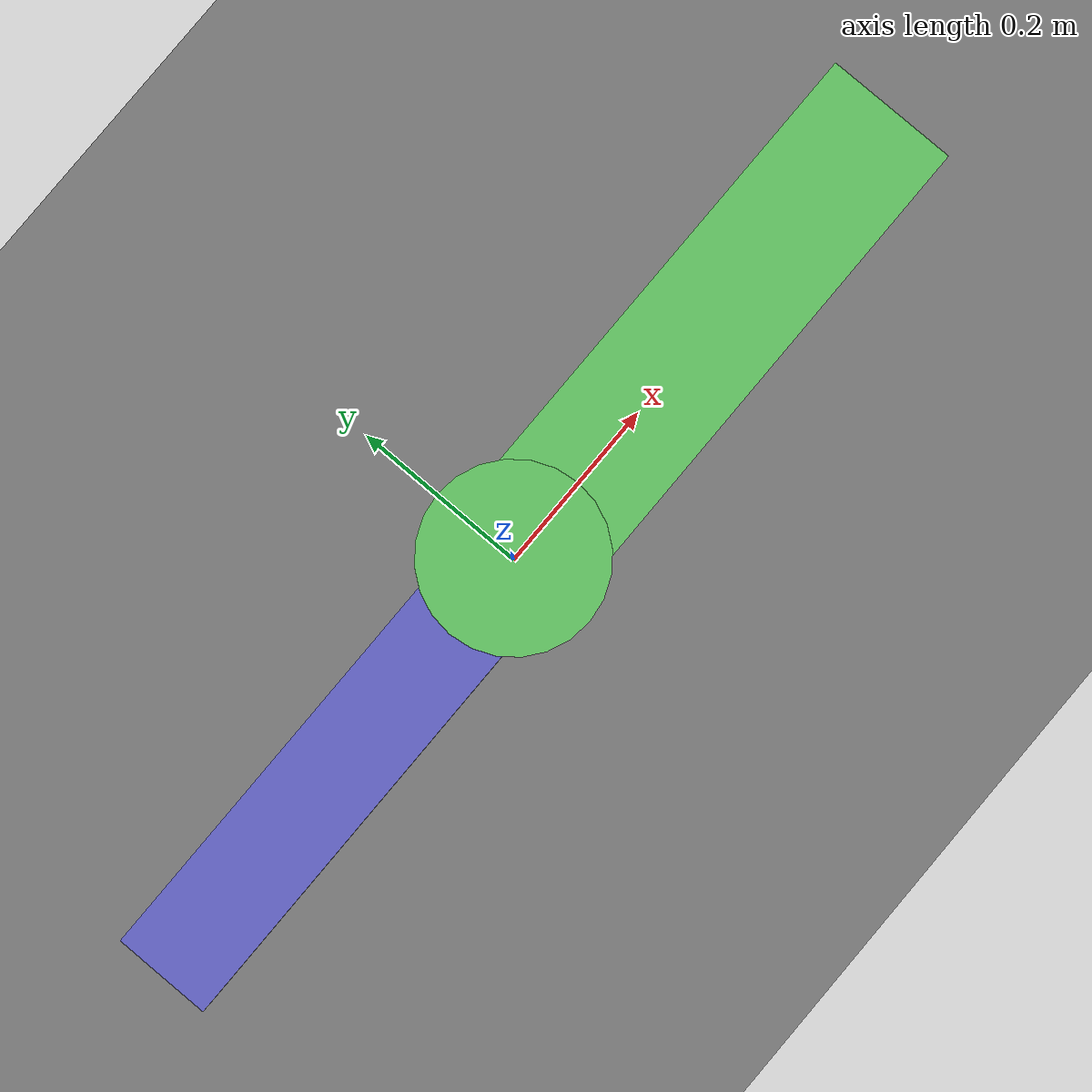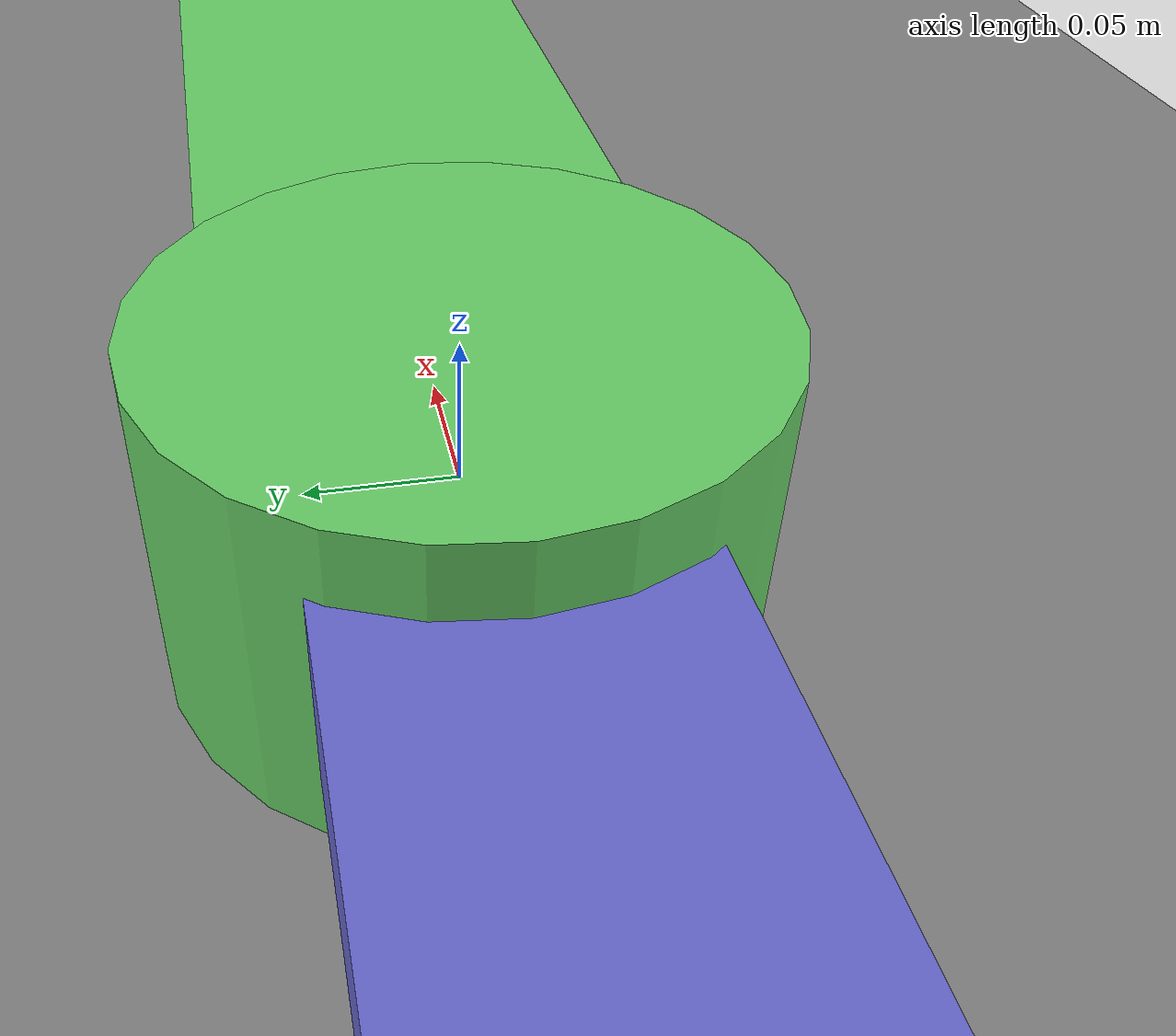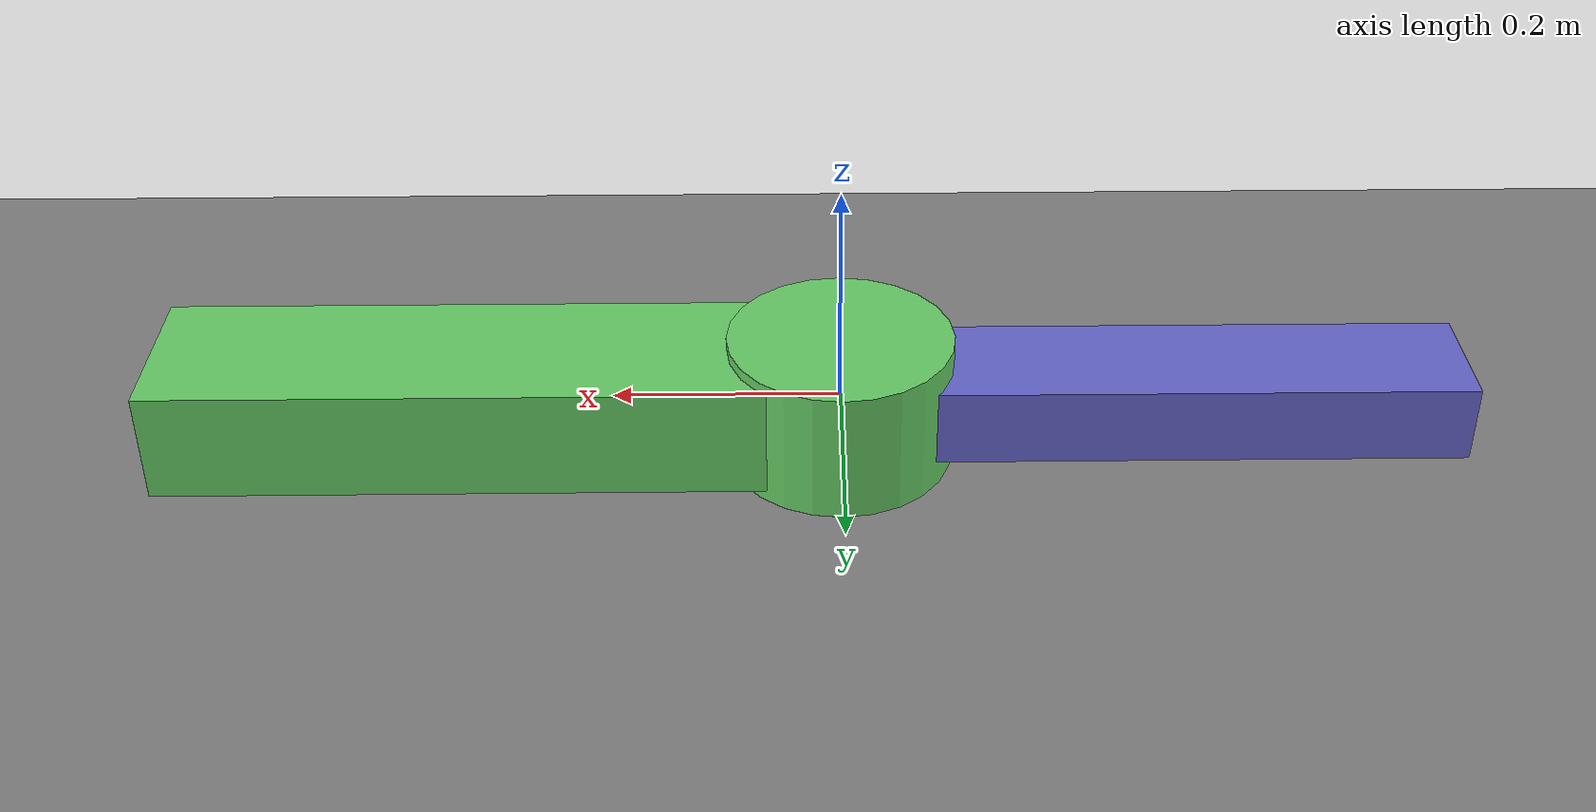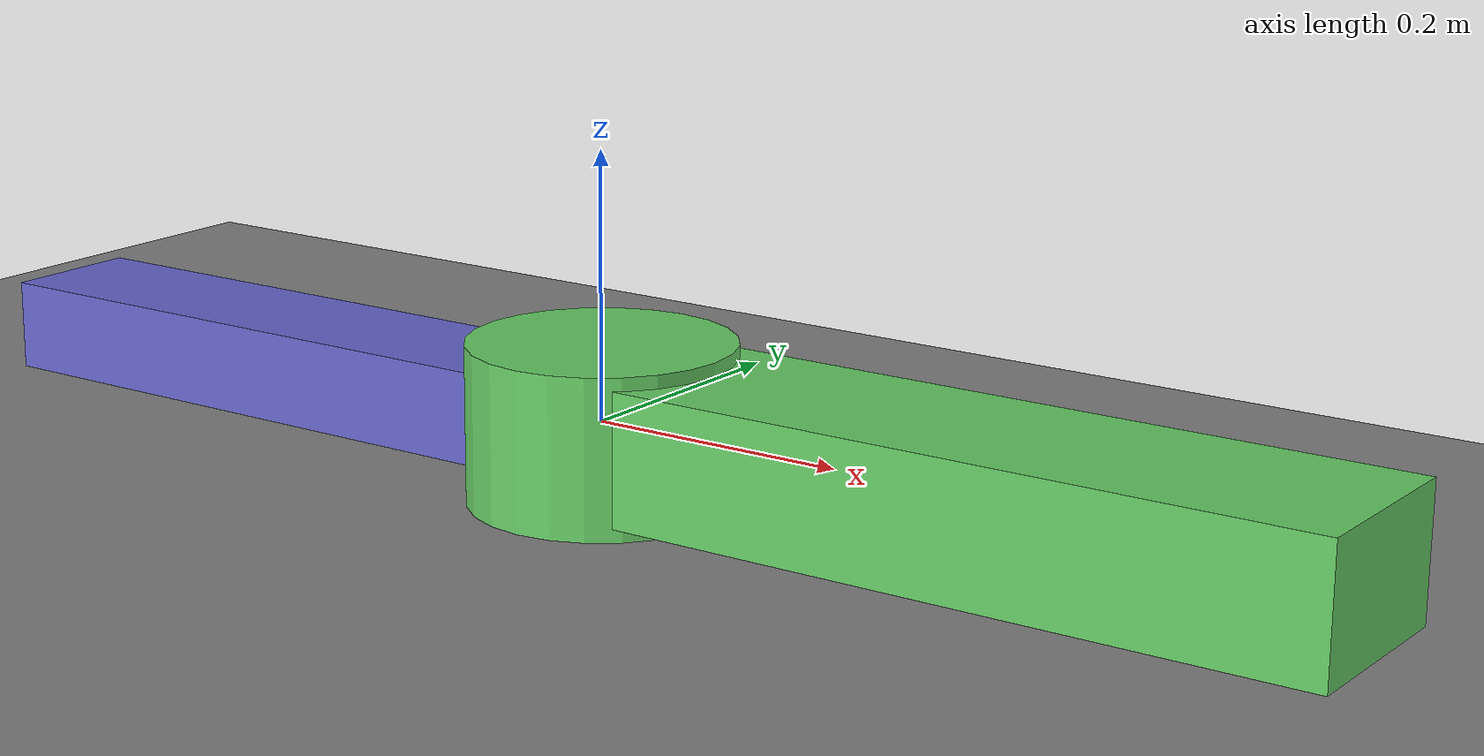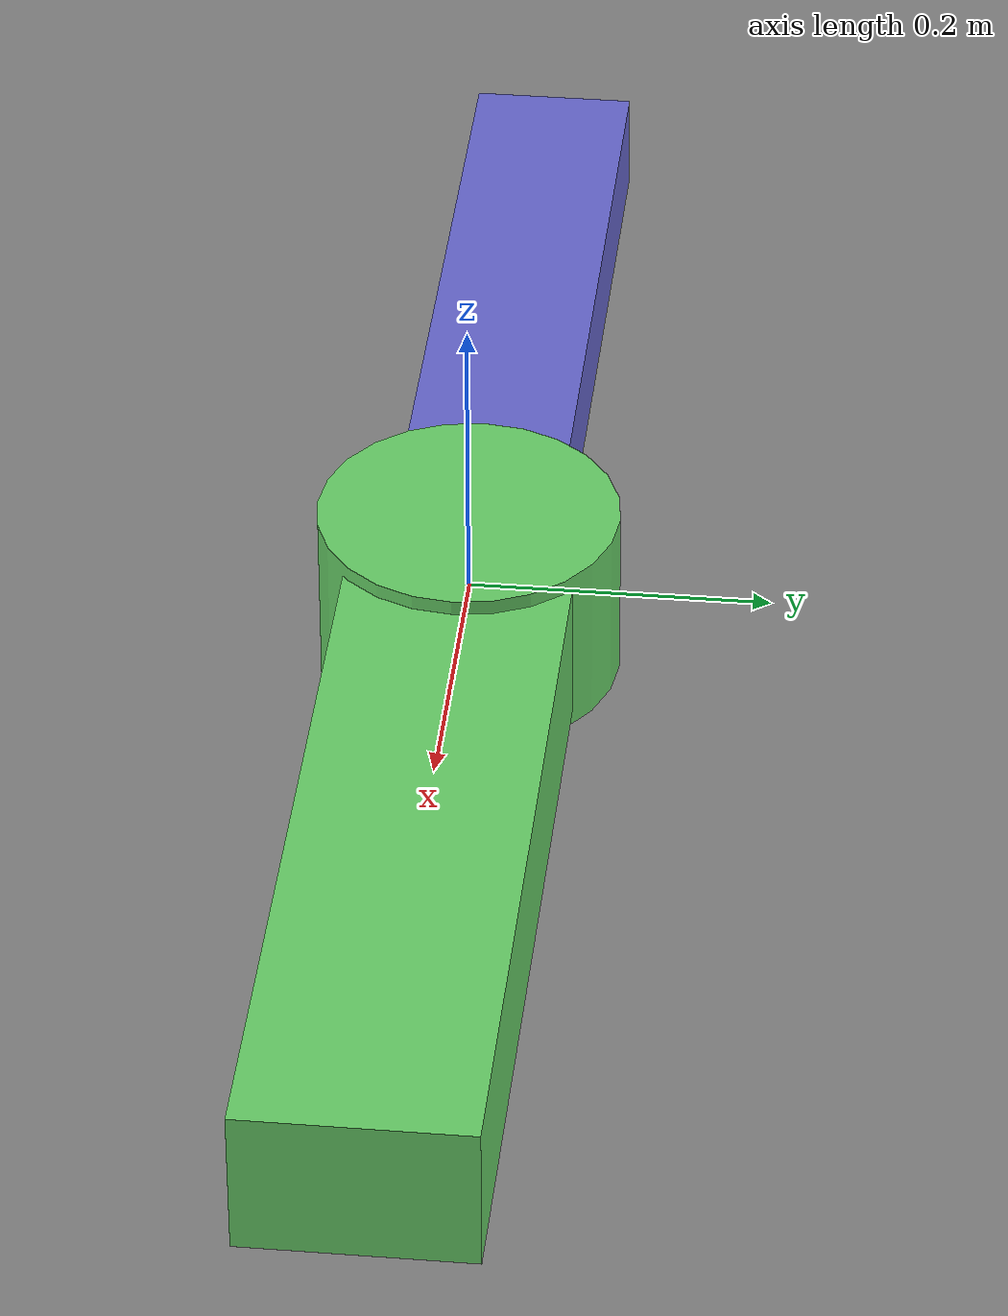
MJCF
<mujoco model='2_FHG_Rob_Model_1'>

  <compiler coordinate='local'/>
  <option timestep='0.002' gravity="0 0 0"/>

  <!-- Anfangspositionen definieren (zum Test) -->
  <keyframe>
    <key name="init_extended" qpos="0 0.9"/>
  </keyframe>

  <worldbody>
    <geom name='floor' pos='0 0 -0.1' size='4 4 4' type='plane' />
    <light name="main_light" pos="0 0 5" dir="0 0 -1" diffuse="1 1 1" specular="0.5 0.5 0.5" />

    <!-- Rotationsgelenk mit starrem Arm -->
    <body name="rotating_arm" pos="0 0 0">
      <joint name="joint1" type="hinge" axis="0 0 1" limited="false"/>
      <geom type="box" size="0.3 0.075 0.05" pos="0.3 0 0" rgba="0.4 0.8 0.4 1"/>
      <geom type="cylinder" size="0.10 0.06" pos="0 0 0" rgba="0.4 0.8 0.4 1"/>

      <inertial pos="0 0 0" mass="0.0001" diaginertia="0.4 0.4 0.4"/>

      <!-- Endmasse -->
      <body name="end_mass" pos="0 0 0">
        <geom type="box" size="0.05 0.07 0.045" pos="0 0 0" rgba="0.4 0.4 0.8 1"/>
        <joint name="joint2" type="slide" axis="1 0 0" limited="false"/>

        <!-- Endeffektor hinzufügen -->
        <site name="end_mass_site" pos="0 0 0" size="0.02" rgba="1 0 0 1"/>

        <inertial pos="0 0 0" mass="2" diaginertia="0.0001 0.0001 0.0001"/>

        <!-- Teleskoparm -->
        <body name="telescopic_link" pos="-0.25 0 0">
          <geom type="box" size="0.3 0.055 0.035" pos="0 0 0" rgba="0.4 0.4 0.8 1"/>

          <inertial pos="0 0 0" mass="5" diaginertia="0.0001 0.0001 0.0001"/>

        </body>
      </body>
    </body>

  <!-- Sites für Ist-Trajektorie einfügen -->
  <body name="sitebody_ist_0" pos="0 0 0">
    <site name="ist_traj_0" type="sphere" size="0.005" rgba="1 0 0 1"/>
  </body>
  <body name="sitebody_ist_1" pos="0 0 0">
    <site name="ist_traj_1" type="sphere" size="0.005" rgba="1 0 0 1"/>
  </body>
  <body name="sitebody_ist_2" pos="0 0 0">
    <site name="ist_traj_2" type="sphere" size="0.005" rgba="1 0 0 1"/>
  </body>
  <body name="sitebody_ist_3" pos="0 0 0">
    <site name="ist_traj_3" type="sphere" size="0.005" rgba="1 0 0 1"/>
  </body>
  <body name="sitebody_ist_4" pos="0 0 0">
    <site name="ist_traj_4" type="sphere" size="0.005" rgba="1 0 0 1"/>
  </body>
  <body name="sitebody_ist_5" pos="0 0 0">
    <site name="ist_traj_5" type="sphere" size="0.005" rgba="1 0 0 1"/>
  </body>
  <body name="sitebody_ist_6" pos="0 0 0">
    <site name="ist_traj_6" type="sphere" size="0.005" rgba="1 0 0 1"/>
  </body>
  <body name="sitebody_ist_7" pos="0 0 0">
    <site name="ist_traj_7" type="sphere" size="0.005" rgba="1 0 0 1"/>
  </body>
  <body name="sitebody_ist_8" pos="0 0 0">
    <site name="ist_traj_8" type="sphere" size="0.005" rgba="1 0 0 1"/>
  </body>
  <body name="sitebody_ist_9" pos="0 0 0">
    <site name="ist_traj_9" type="sphere" size="0.005" rgba="1 0 0 1"/>
  </body>
  <body name="sitebody_ist_10" pos="0 0 0">
    <site name="ist_traj_10" type="sphere" size="0.005" rgba="1 0 0 1"/>
  </body>
  <body name="sitebody_ist_11" pos="0 0 0">
    <site name="ist_traj_11" type="sphere" size="0.005" rgba="1 0 0 1"/>
  </body>
  <body name="sitebody_ist_12" pos="0 0 0">
    <site name="ist_traj_12" type="sphere" size="0.005" rgba="1 0 0 1"/>
  </body>
  <body name="sitebody_ist_13" pos="0 0 0">
    <site name="ist_traj_13" type="sphere" size="0.005" rgba="1 0 0 1"/>
  </body>
  <body name="sitebody_ist_14" pos="0 0 0">
    <site name="ist_traj_14" type="sphere" size="0.005" rgba="1 0 0 1"/>
  </body>
  <body name="sitebody_ist_15" pos="0 0 0">
    <site name="ist_traj_15" type="sphere" size="0.005" rgba="1 0 0 1"/>
  </body>
  <body name="sitebody_ist_16" pos="0 0 0">
    <site name="ist_traj_16" type="sphere" size="0.005" rgba="1 0 0 1"/>
  </body>
  <body name="sitebody_ist_17" pos="0 0 0">
    <site name="ist_traj_17" type="sphere" size="0.005" rgba="1 0 0 1"/>
  </body>
  <body name="sitebody_ist_18" pos="0 0 0">
    <site name="ist_traj_18" type="sphere" size="0.005" rgba="1 0 0 1"/>
  </body>
  <body name="sitebody_ist_19" pos="0 0 0">
    <site name="ist_traj_19" type="sphere" size="0.005" rgba="1 0 0 1"/>
  </body>
  <body name="sitebody_ist_20" pos="0 0 0">
    <site name="ist_traj_20" type="sphere" size="0.005" rgba="1 0 0 1"/>
  </body>
  <body name="sitebody_ist_21" pos="0 0 0">
    <site name="ist_traj_21" type="sphere" size="0.005" rgba="1 0 0 1"/>
  </body>
  <body name="sitebody_ist_22" pos="0 0 0">
    <site name="ist_traj_22" type="sphere" size="0.005" rgba="1 0 0 1"/>
  </body>
  <body name="sitebody_ist_23" pos="0 0 0">
    <site name="ist_traj_23" type="sphere" size="0.005" rgba="1 0 0 1"/>
  </body>
  <body name="sitebody_ist_24" pos="0 0 0">
    <site name="ist_traj_24" type="sphere" size="0.005" rgba="1 0 0 1"/>
  </body>
  <body name="sitebody_ist_25" pos="0 0 0">
    <site name="ist_traj_25" type="sphere" size="0.005" rgba="1 0 0 1"/>
  </body>
  <body name="sitebody_ist_26" pos="0 0 0">
    <site name="ist_traj_26" type="sphere" size="0.005" rgba="1 0 0 1"/>
  </body>
  <body name="sitebody_ist_27" pos="0 0 0">
    <site name="ist_traj_27" type="sphere" size="0.005" rgba="1 0 0 1"/>
  </body>
  <body name="sitebody_ist_28" pos="0 0 0">
    <site name="ist_traj_28" type="sphere" size="0.005" rgba="1 0 0 1"/>
  </body>
  <body name="sitebody_ist_29" pos="0 0 0">
    <site name="ist_traj_29" type="sphere" size="0.005" rgba="1 0 0 1"/>
  </body>
  <body name="sitebody_ist_30" pos="0 0 0">
    <site name="ist_traj_30" type="sphere" size="0.005" rgba="1 0 0 1"/>
  </body>
  <body name="sitebody_ist_31" pos="0 0 0">
    <site name="ist_traj_31" type="sphere" size="0.005" rgba="1 0 0 1"/>
  </body>
  <body name="sitebody_ist_32" pos="0 0 0">
    <site name="ist_traj_32" type="sphere" size="0.005" rgba="1 0 0 1"/>
  </body>
  <body name="sitebody_ist_33" pos="0 0 0">
    <site name="ist_traj_33" type="sphere" size="0.005" rgba="1 0 0 1"/>
  </body>
  <body name="sitebody_ist_34" pos="0 0 0">
    <site name="ist_traj_34" type="sphere" size="0.005" rgba="1 0 0 1"/>
  </body>
  <body name="sitebody_ist_35" pos="0 0 0">
    <site name="ist_traj_35" type="sphere" size="0.005" rgba="1 0 0 1"/>
  </body>
  <body name="sitebody_ist_36" pos="0 0 0">
    <site name="ist_traj_36" type="sphere" size="0.005" rgba="1 0 0 1"/>
  </body>
  <body name="sitebody_ist_37" pos="0 0 0">
    <site name="ist_traj_37" type="sphere" size="0.005" rgba="1 0 0 1"/>
  </body>
  <body name="sitebody_ist_38" pos="0 0 0">
    <site name="ist_traj_38" type="sphere" size="0.005" rgba="1 0 0 1"/>
  </body>
  <body name="sitebody_ist_39" pos="0 0 0">
    <site name="ist_traj_39" type="sphere" size="0.005" rgba="1 0 0 1"/>
  </body>
  <body name="sitebody_ist_40" pos="0 0 0">
    <site name="ist_traj_40" type="sphere" size="0.005" rgba="1 0 0 1"/>
  </body>
  <body name="sitebody_ist_41" pos="0 0 0">
    <site name="ist_traj_41" type="sphere" size="0.005" rgba="1 0 0 1"/>
  </body>
  <body name="sitebody_ist_42" pos="0 0 0">
    <site name="ist_traj_42" type="sphere" size="0.005" rgba="1 0 0 1"/>
  </body>
  <body name="sitebody_ist_43" pos="0 0 0">
    <site name="ist_traj_43" type="sphere" size="0.005" rgba="1 0 0 1"/>
  </body>
  <body name="sitebody_ist_44" pos="0 0 0">
    <site name="ist_traj_44" type="sphere" size="0.005" rgba="1 0 0 1"/>
  </body>
  <body name="sitebody_ist_45" pos="0 0 0">
    <site name="ist_traj_45" type="sphere" size="0.005" rgba="1 0 0 1"/>
  </body>
  <body name="sitebody_ist_46" pos="0 0 0">
    <site name="ist_traj_46" type="sphere" size="0.005" rgba="1 0 0 1"/>
  </body>
  <body name="sitebody_ist_47" pos="0 0 0">
    <site name="ist_traj_47" type="sphere" size="0.005" rgba="1 0 0 1"/>
  </body>
  <body name="sitebody_ist_48" pos="0 0 0">
    <site name="ist_traj_48" type="sphere" size="0.005" rgba="1 0 0 1"/>
  </body>
  <body name="sitebody_ist_49" pos="0 0 0">
    <site name="ist_traj_49" type="sphere" size="0.005" rgba="1 0 0 1"/>
  </body>
  <body name="sitebody_ist_50" pos="0 0 0">
    <site name="ist_traj_50" type="sphere" size="0.005" rgba="1 0 0 1"/>
  </body>
  <body name="sitebody_ist_51" pos="0 0 0">
    <site name="ist_traj_51" type="sphere" size="0.005" rgba="1 0 0 1"/>
  </body>
  <body name="sitebody_ist_52" pos="0 0 0">
    <site name="ist_traj_52" type="sphere" size="0.005" rgba="1 0 0 1"/>
  </body>
  <body name="sitebody_ist_53" pos="0 0 0">
    <site name="ist_traj_53" type="sphere" size="0.005" rgba="1 0 0 1"/>
  </body>
  <body name="sitebody_ist_54" pos="0 0 0">
    <site name="ist_traj_54" type="sphere" size="0.005" rgba="1 0 0 1"/>
  </body>
  <body name="sitebody_ist_55" pos="0 0 0">
    <site name="ist_traj_55" type="sphere" size="0.005" rgba="1 0 0 1"/>
  </body>
  <body name="sitebody_ist_56" pos="0 0 0">
    <site name="ist_traj_56" type="sphere" size="0.005" rgba="1 0 0 1"/>
  </body>
  <body name="sitebody_ist_57" pos="0 0 0">
    <site name="ist_traj_57" type="sphere" size="0.005" rgba="1 0 0 1"/>
  </body>
  <body name="sitebody_ist_58" pos="0 0 0">
    <site name="ist_traj_58" type="sphere" size="0.005" rgba="1 0 0 1"/>
  </body>
  <body name="sitebody_ist_59" pos="0 0 0">
    <site name="ist_traj_59" type="sphere" size="0.005" rgba="1 0 0 1"/>
  </body>
  <body name="sitebody_ist_60" pos="0 0 0">
    <site name="ist_traj_60" type="sphere" size="0.005" rgba="1 0 0 1"/>
  </body>
  <body name="sitebody_ist_61" pos="0 0 0">
    <site name="ist_traj_61" type="sphere" size="0.005" rgba="1 0 0 1"/>
  </body>
  <body name="sitebody_ist_62" pos="0 0 0">
    <site name="ist_traj_62" type="sphere" size="0.005" rgba="1 0 0 1"/>
  </body>
  <body name="sitebody_ist_63" pos="0 0 0">
    <site name="ist_traj_63" type="sphere" size="0.005" rgba="1 0 0 1"/>
  </body>
  <body name="sitebody_ist_64" pos="0 0 0">
    <site name="ist_traj_64" type="sphere" size="0.005" rgba="1 0 0 1"/>
  </body>
  <body name="sitebody_ist_65" pos="0 0 0">
    <site name="ist_traj_65" type="sphere" size="0.005" rgba="1 0 0 1"/>
  </body>
  <body name="sitebody_ist_66" pos="0 0 0">
    <site name="ist_traj_66" type="sphere" size="0.005" rgba="1 0 0 1"/>
  </body>
  <body name="sitebody_ist_67" pos="0 0 0">
    <site name="ist_traj_67" type="sphere" size="0.005" rgba="1 0 0 1"/>
  </body>
  <body name="sitebody_ist_68" pos="0 0 0">
    <site name="ist_traj_68" type="sphere" size="0.005" rgba="1 0 0 1"/>
  </body>
  <body name="sitebody_ist_69" pos="0 0 0">
    <site name="ist_traj_69" type="sphere" size="0.005" rgba="1 0 0 1"/>
  </body>
  <body name="sitebody_ist_70" pos="0 0 0">
    <site name="ist_traj_70" type="sphere" size="0.005" rgba="1 0 0 1"/>
  </body>
  <body name="sitebody_ist_71" pos="0 0 0">
    <site name="ist_traj_71" type="sphere" size="0.005" rgba="1 0 0 1"/>
  </body>
  <body name="sitebody_ist_72" pos="0 0 0">
    <site name="ist_traj_72" type="sphere" size="0.005" rgba="1 0 0 1"/>
  </body>
  <body name="sitebody_ist_73" pos="0 0 0">
    <site name="ist_traj_73" type="sphere" size="0.005" rgba="1 0 0 1"/>
  </body>
  <body name="sitebody_ist_74" pos="0 0 0">
    <site name="ist_traj_74" type="sphere" size="0.005" rgba="1 0 0 1"/>
  </body>
  <body name="sitebody_ist_75" pos="0 0 0">
    <site name="ist_traj_75" type="sphere" size="0.005" rgba="1 0 0 1"/>
  </body>
  <body name="sitebody_ist_76" pos="0 0 0">
    <site name="ist_traj_76" type="sphere" size="0.005" rgba="1 0 0 1"/>
  </body>
  <body name="sitebody_ist_77" pos="0 0 0">
    <site name="ist_traj_77" type="sphere" size="0.005" rgba="1 0 0 1"/>
  </body>
  <body name="sitebody_ist_78" pos="0 0 0">
    <site name="ist_traj_78" type="sphere" size="0.005" rgba="1 0 0 1"/>
  </body>
  <body name="sitebody_ist_79" pos="0 0 0">
    <site name="ist_traj_79" type="sphere" size="0.005" rgba="1 0 0 1"/>
  </body>
  <body name="sitebody_ist_80" pos="0 0 0">
    <site name="ist_traj_80" type="sphere" size="0.005" rgba="1 0 0 1"/>
  </body>
  <body name="sitebody_ist_81" pos="0 0 0">
    <site name="ist_traj_81" type="sphere" size="0.005" rgba="1 0 0 1"/>
  </body>
  <body name="sitebody_ist_82" pos="0 0 0">
    <site name="ist_traj_82" type="sphere" size="0.005" rgba="1 0 0 1"/>
  </body>
  <body name="sitebody_ist_83" pos="0 0 0">
    <site name="ist_traj_83" type="sphere" size="0.005" rgba="1 0 0 1"/>
  </body>
  <body name="sitebody_ist_84" pos="0 0 0">
    <site name="ist_traj_84" type="sphere" size="0.005" rgba="1 0 0 1"/>
  </body>
  <body name="sitebody_ist_85" pos="0 0 0">
    <site name="ist_traj_85" type="sphere" size="0.005" rgba="1 0 0 1"/>
  </body>
  <body name="sitebody_ist_86" pos="0 0 0">
    <site name="ist_traj_86" type="sphere" size="0.005" rgba="1 0 0 1"/>
  </body>
  <body name="sitebody_ist_87" pos="0 0 0">
    <site name="ist_traj_87" type="sphere" size="0.005" rgba="1 0 0 1"/>
  </body>
  <body name="sitebody_ist_88" pos="0 0 0">
    <site name="ist_traj_88" type="sphere" size="0.005" rgba="1 0 0 1"/>
  </body>
  <body name="sitebody_ist_89" pos="0 0 0">
    <site name="ist_traj_89" type="sphere" size="0.005" rgba="1 0 0 1"/>
  </body>
  <body name="sitebody_ist_90" pos="0 0 0">
    <site name="ist_traj_90" type="sphere" size="0.005" rgba="1 0 0 1"/>
  </body>
  <body name="sitebody_ist_91" pos="0 0 0">
    <site name="ist_traj_91" type="sphere" size="0.005" rgba="1 0 0 1"/>
  </body>
  <body name="sitebody_ist_92" pos="0 0 0">
    <site name="ist_traj_92" type="sphere" size="0.005" rgba="1 0 0 1"/>
  </body>
  <body name="sitebody_ist_93" pos="0 0 0">
    <site name="ist_traj_93" type="sphere" size="0.005" rgba="1 0 0 1"/>
  </body>
  <body name="sitebody_ist_94" pos="0 0 0">
    <site name="ist_traj_94" type="sphere" size="0.005" rgba="1 0 0 1"/>
  </body>
  <body name="sitebody_ist_95" pos="0 0 0">
    <site name="ist_traj_95" type="sphere" size="0.005" rgba="1 0 0 1"/>
  </body>
  <body name="sitebody_ist_96" pos="0 0 0">
    <site name="ist_traj_96" type="sphere" size="0.005" rgba="1 0 0 1"/>
  </body>
  <body name="sitebody_ist_97" pos="0 0 0">
    <site name="ist_traj_97" type="sphere" size="0.005" rgba="1 0 0 1"/>
  </body>
  <body name="sitebody_ist_98" pos="0 0 0">
    <site name="ist_traj_98" type="sphere" size="0.005" rgba="1 0 0 1"/>
  </body>
  <body name="sitebody_ist_99" pos="0 0 0">
    <site name="ist_traj_99" type="sphere" size="0.005" rgba="1 0 0 1"/>
  </body>
  <body name="sitebody_ist_100" pos="0 0 0">
    <site name="ist_traj_100" type="sphere" size="0.005" rgba="1 0 0 1"/>
  </body>
  <body name="sitebody_ist_101" pos="0 0 0">
    <site name="ist_traj_101" type="sphere" size="0.005" rgba="1 0 0 1"/>
  </body>
  <body name="sitebody_ist_102" pos="0 0 0">
    <site name="ist_traj_102" type="sphere" size="0.005" rgba="1 0 0 1"/>
  </body>
  <body name="sitebody_ist_103" pos="0 0 0">
    <site name="ist_traj_103" type="sphere" size="0.005" rgba="1 0 0 1"/>
  </body>
  <body name="sitebody_ist_104" pos="0 0 0">
    <site name="ist_traj_104" type="sphere" size="0.005" rgba="1 0 0 1"/>
  </body>
  <body name="sitebody_ist_105" pos="0 0 0">
    <site name="ist_traj_105" type="sphere" size="0.005" rgba="1 0 0 1"/>
  </body>
  <body name="sitebody_ist_106" pos="0 0 0">
    <site name="ist_traj_106" type="sphere" size="0.005" rgba="1 0 0 1"/>
  </body>
  <body name="sitebody_ist_107" pos="0 0 0">
    <site name="ist_traj_107" type="sphere" size="0.005" rgba="1 0 0 1"/>
  </body>
  <body name="sitebody_ist_108" pos="0 0 0">
    <site name="ist_traj_108" type="sphere" size="0.005" rgba="1 0 0 1"/>
  </body>
  <body name="sitebody_ist_109" pos="0 0 0">
    <site name="ist_traj_109" type="sphere" size="0.005" rgba="1 0 0 1"/>
  </body>
  <body name="sitebody_ist_110" pos="0 0 0">
    <site name="ist_traj_110" type="sphere" size="0.005" rgba="1 0 0 1"/>
  </body>
  <body name="sitebody_ist_111" pos="0 0 0">
    <site name="ist_traj_111" type="sphere" size="0.005" rgba="1 0 0 1"/>
  </body>
  <body name="sitebody_ist_112" pos="0 0 0">
    <site name="ist_traj_112" type="sphere" size="0.005" rgba="1 0 0 1"/>
  </body>
  <body name="sitebody_ist_113" pos="0 0 0">
    <site name="ist_traj_113" type="sphere" size="0.005" rgba="1 0 0 1"/>
  </body>
  <body name="sitebody_ist_114" pos="0 0 0">
    <site name="ist_traj_114" type="sphere" size="0.005" rgba="1 0 0 1"/>
  </body>
  <body name="sitebody_ist_115" pos="0 0 0">
    <site name="ist_traj_115" type="sphere" size="0.005" rgba="1 0 0 1"/>
  </body>
  <body name="sitebody_ist_116" pos="0 0 0">
    <site name="ist_traj_116" type="sphere" size="0.005" rgba="1 0 0 1"/>
  </body>
  <body name="sitebody_ist_117" pos="0 0 0">
    <site name="ist_traj_117" type="sphere" size="0.005" rgba="1 0 0 1"/>
  </body>
  <body name="sitebody_ist_118" pos="0 0 0">
    <site name="ist_traj_118" type="sphere" size="0.005" rgba="1 0 0 1"/>
  </body>
  <body name="sitebody_ist_119" pos="0 0 0">
    <site name="ist_traj_119" type="sphere" size="0.005" rgba="1 0 0 1"/>
  </body>
  <body name="sitebody_ist_120" pos="0 0 0">
    <site name="ist_traj_120" type="sphere" size="0.005" rgba="1 0 0 1"/>
  </body>
  <body name="sitebody_ist_121" pos="0 0 0">
    <site name="ist_traj_121" type="sphere" size="0.005" rgba="1 0 0 1"/>
  </body>
  <body name="sitebody_ist_122" pos="0 0 0">
    <site name="ist_traj_122" type="sphere" size="0.005" rgba="1 0 0 1"/>
  </body>
  <body name="sitebody_ist_123" pos="0 0 0">
    <site name="ist_traj_123" type="sphere" size="0.005" rgba="1 0 0 1"/>
  </body>
  <body name="sitebody_ist_124" pos="0 0 0">
    <site name="ist_traj_124" type="sphere" size="0.005" rgba="1 0 0 1"/>
  </body>
  <body name="sitebody_ist_125" pos="0 0 0">
    <site name="ist_traj_125" type="sphere" size="0.005" rgba="1 0 0 1"/>
  </body>
  <body name="sitebody_ist_126" pos="0 0 0">
    <site name="ist_traj_126" type="sphere" size="0.005" rgba="1 0 0 1"/>
  </body>
  <body name="sitebody_ist_127" pos="0 0 0">
    <site name="ist_traj_127" type="sphere" size="0.005" rgba="1 0 0 1"/>
  </body>
  <body name="sitebody_ist_128" pos="0 0 0">
    <site name="ist_traj_128" type="sphere" size="0.005" rgba="1 0 0 1"/>
  </body>
  <body name="sitebody_ist_129" pos="0 0 0">
    <site name="ist_traj_129" type="sphere" size="0.005" rgba="1 0 0 1"/>
  </body>
  <body name="sitebody_ist_130" pos="0 0 0">
    <site name="ist_traj_130" type="sphere" size="0.005" rgba="1 0 0 1"/>
  </body>
  <body name="sitebody_ist_131" pos="0 0 0">
    <site name="ist_traj_131" type="sphere" size="0.005" rgba="1 0 0 1"/>
  </body>
  <body name="sitebody_ist_132" pos="0 0 0">
    <site name="ist_traj_132" type="sphere" size="0.005" rgba="1 0 0 1"/>
  </body>
  <body name="sitebody_ist_133" pos="0 0 0">
    <site name="ist_traj_133" type="sphere" size="0.005" rgba="1 0 0 1"/>
  </body>
  <body name="sitebody_ist_134" pos="0 0 0">
    <site name="ist_traj_134" type="sphere" size="0.005" rgba="1 0 0 1"/>
  </body>
  <body name="sitebody_ist_135" pos="0 0 0">
    <site name="ist_traj_135" type="sphere" size="0.005" rgba="1 0 0 1"/>
  </body>
  <body name="sitebody_ist_136" pos="0 0 0">
    <site name="ist_traj_136" type="sphere" size="0.005" rgba="1 0 0 1"/>
  </body>
  <body name="sitebody_ist_137" pos="0 0 0">
    <site name="ist_traj_137" type="sphere" size="0.005" rgba="1 0 0 1"/>
  </body>
  <body name="sitebody_ist_138" pos="0 0 0">
    <site name="ist_traj_138" type="sphere" size="0.005" rgba="1 0 0 1"/>
  </body>
  <body name="sitebody_ist_139" pos="0 0 0">
    <site name="ist_traj_139" type="sphere" size="0.005" rgba="1 0 0 1"/>
  </body>
  <body name="sitebody_ist_140" pos="0 0 0">
    <site name="ist_traj_140" type="sphere" size="0.005" rgba="1 0 0 1"/>
  </body>
  <body name="sitebody_ist_141" pos="0 0 0">
    <site name="ist_traj_141" type="sphere" size="0.005" rgba="1 0 0 1"/>
  </body>
  <body name="sitebody_ist_142" pos="0 0 0">
    <site name="ist_traj_142" type="sphere" size="0.005" rgba="1 0 0 1"/>
  </body>
  <body name="sitebody_ist_143" pos="0 0 0">
    <site name="ist_traj_143" type="sphere" size="0.005" rgba="1 0 0 1"/>
  </body>
  <body name="sitebody_ist_144" pos="0 0 0">
    <site name="ist_traj_144" type="sphere" size="0.005" rgba="1 0 0 1"/>
  </body>
  <body name="sitebody_ist_145" pos="0 0 0">
    <site name="ist_traj_145" type="sphere" size="0.005" rgba="1 0 0 1"/>
  </body>
  <body name="sitebody_ist_146" pos="0 0 0">
    <site name="ist_traj_146" type="sphere" size="0.005" rgba="1 0 0 1"/>
  </body>
  <body name="sitebody_ist_147" pos="0 0 0">
    <site name="ist_traj_147" type="sphere" size="0.005" rgba="1 0 0 1"/>
  </body>
  <body name="sitebody_ist_148" pos="0 0 0">
    <site name="ist_traj_148" type="sphere" size="0.005" rgba="1 0 0 1"/>
  </body>
  <body name="sitebody_ist_149" pos="0 0 0">
    <site name="ist_traj_149" type="sphere" size="0.005" rgba="1 0 0 1"/>
  </body>
  <body name="sitebody_ist_150" pos="0 0 0">
    <site name="ist_traj_150" type="sphere" size="0.005" rgba="1 0 0 1"/>
  </body>
  <body name="sitebody_ist_151" pos="0 0 0">
    <site name="ist_traj_151" type="sphere" size="0.005" rgba="1 0 0 1"/>
  </body>
  <body name="sitebody_ist_152" pos="0 0 0">
    <site name="ist_traj_152" type="sphere" size="0.005" rgba="1 0 0 1"/>
  </body>
  <body name="sitebody_ist_153" pos="0 0 0">
    <site name="ist_traj_153" type="sphere" size="0.005" rgba="1 0 0 1"/>
  </body>
  <body name="sitebody_ist_154" pos="0 0 0">
    <site name="ist_traj_154" type="sphere" size="0.005" rgba="1 0 0 1"/>
  </body>
  <body name="sitebody_ist_155" pos="0 0 0">
    <site name="ist_traj_155" type="sphere" size="0.005" rgba="1 0 0 1"/>
  </body>
  <body name="sitebody_ist_156" pos="0 0 0">
    <site name="ist_traj_156" type="sphere" size="0.005" rgba="1 0 0 1"/>
  </body>
  <body name="sitebody_ist_157" pos="0 0 0">
    <site name="ist_traj_157" type="sphere" size="0.005" rgba="1 0 0 1"/>
  </body>
  <body name="sitebody_ist_158" pos="0 0 0">
    <site name="ist_traj_158" type="sphere" size="0.005" rgba="1 0 0 1"/>
  </body>
  <body name="sitebody_ist_159" pos="0 0 0">
    <site name="ist_traj_159" type="sphere" size="0.005" rgba="1 0 0 1"/>
  </body>
  <body name="sitebody_ist_160" pos="0 0 0">
    <site name="ist_traj_160" type="sphere" size="0.005" rgba="1 0 0 1"/>
  </body>
  <body name="sitebody_ist_161" pos="0 0 0">
    <site name="ist_traj_161" type="sphere" size="0.005" rgba="1 0 0 1"/>
  </body>
  <body name="sitebody_ist_162" pos="0 0 0">
    <site name="ist_traj_162" type="sphere" size="0.005" rgba="1 0 0 1"/>
  </body>
  <body name="sitebody_ist_163" pos="0 0 0">
    <site name="ist_traj_163" type="sphere" size="0.005" rgba="1 0 0 1"/>
  </body>
  <body name="sitebody_ist_164" pos="0 0 0">
    <site name="ist_traj_164" type="sphere" size="0.005" rgba="1 0 0 1"/>
  </body>
  <body name="sitebody_ist_165" pos="0 0 0">
    <site name="ist_traj_165" type="sphere" size="0.005" rgba="1 0 0 1"/>
  </body>
  <body name="sitebody_ist_166" pos="0 0 0">
    <site name="ist_traj_166" type="sphere" size="0.005" rgba="1 0 0 1"/>
  </body>
  <body name="sitebody_ist_167" pos="0 0 0">
    <site name="ist_traj_167" type="sphere" size="0.005" rgba="1 0 0 1"/>
  </body>
  <body name="sitebody_ist_168" pos="0 0 0">
    <site name="ist_traj_168" type="sphere" size="0.005" rgba="1 0 0 1"/>
  </body>
  <body name="sitebody_ist_169" pos="0 0 0">
    <site name="ist_traj_169" type="sphere" size="0.005" rgba="1 0 0 1"/>
  </body>
  <body name="sitebody_ist_170" pos="0 0 0">
    <site name="ist_traj_170" type="sphere" size="0.005" rgba="1 0 0 1"/>
  </body>
  <body name="sitebody_ist_171" pos="0 0 0">
    <site name="ist_traj_171" type="sphere" size="0.005" rgba="1 0 0 1"/>
  </body>
  <body name="sitebody_ist_172" pos="0 0 0">
    <site name="ist_traj_172" type="sphere" size="0.005" rgba="1 0 0 1"/>
  </body>
  <body name="sitebody_ist_173" pos="0 0 0">
    <site name="ist_traj_173" type="sphere" size="0.005" rgba="1 0 0 1"/>
  </body>
  <body name="sitebody_ist_174" pos="0 0 0">
    <site name="ist_traj_174" type="sphere" size="0.005" rgba="1 0 0 1"/>
  </body>
  <body name="sitebody_ist_175" pos="0 0 0">
    <site name="ist_traj_175" type="sphere" size="0.005" rgba="1 0 0 1"/>
  </body>
  <body name="sitebody_ist_176" pos="0 0 0">
    <site name="ist_traj_176" type="sphere" size="0.005" rgba="1 0 0 1"/>
  </body>
  <body name="sitebody_ist_177" pos="0 0 0">
    <site name="ist_traj_177" type="sphere" size="0.005" rgba="1 0 0 1"/>
  </body>
  <body name="sitebody_ist_178" pos="0 0 0">
    <site name="ist_traj_178" type="sphere" size="0.005" rgba="1 0 0 1"/>
  </body>
  <body name="sitebody_ist_179" pos="0 0 0">
    <site name="ist_traj_179" type="sphere" size="0.005" rgba="1 0 0 1"/>
  </body>
  <body name="sitebody_ist_180" pos="0 0 0">
    <site name="ist_traj_180" type="sphere" size="0.005" rgba="1 0 0 1"/>
  </body>
  <body name="sitebody_ist_181" pos="0 0 0">
    <site name="ist_traj_181" type="sphere" size="0.005" rgba="1 0 0 1"/>
  </body>
  <body name="sitebody_ist_182" pos="0 0 0">
    <site name="ist_traj_182" type="sphere" size="0.005" rgba="1 0 0 1"/>
  </body>
  <body name="sitebody_ist_183" pos="0 0 0">
    <site name="ist_traj_183" type="sphere" size="0.005" rgba="1 0 0 1"/>
  </body>
  <body name="sitebody_ist_184" pos="0 0 0">
    <site name="ist_traj_184" type="sphere" size="0.005" rgba="1 0 0 1"/>
  </body>
  <body name="sitebody_ist_185" pos="0 0 0">
    <site name="ist_traj_185" type="sphere" size="0.005" rgba="1 0 0 1"/>
  </body>
  <body name="sitebody_ist_186" pos="0 0 0">
    <site name="ist_traj_186" type="sphere" size="0.005" rgba="1 0 0 1"/>
  </body>
  <body name="sitebody_ist_187" pos="0 0 0">
    <site name="ist_traj_187" type="sphere" size="0.005" rgba="1 0 0 1"/>
  </body>
  <body name="sitebody_ist_188" pos="0 0 0">
    <site name="ist_traj_188" type="sphere" size="0.005" rgba="1 0 0 1"/>
  </body>
  <body name="sitebody_ist_189" pos="0 0 0">
    <site name="ist_traj_189" type="sphere" size="0.005" rgba="1 0 0 1"/>
  </body>
  <body name="sitebody_ist_190" pos="0 0 0">
    <site name="ist_traj_190" type="sphere" size="0.005" rgba="1 0 0 1"/>
  </body>
  <body name="sitebody_ist_191" pos="0 0 0">
    <site name="ist_traj_191" type="sphere" size="0.005" rgba="1 0 0 1"/>
  </body>
  <body name="sitebody_ist_192" pos="0 0 0">
    <site name="ist_traj_192" type="sphere" size="0.005" rgba="1 0 0 1"/>
  </body>
  <body name="sitebody_ist_193" pos="0 0 0">
    <site name="ist_traj_193" type="sphere" size="0.005" rgba="1 0 0 1"/>
  </body>
  <body name="sitebody_ist_194" pos="0 0 0">
    <site name="ist_traj_194" type="sphere" size="0.005" rgba="1 0 0 1"/>
  </body>
  <body name="sitebody_ist_195" pos="0 0 0">
    <site name="ist_traj_195" type="sphere" size="0.005" rgba="1 0 0 1"/>
  </body>
  <body name="sitebody_ist_196" pos="0 0 0">
    <site name="ist_traj_196" type="sphere" size="0.005" rgba="1 0 0 1"/>
  </body>
  <body name="sitebody_ist_197" pos="0 0 0">
    <site name="ist_traj_197" type="sphere" size="0.005" rgba="1 0 0 1"/>
  </body>
  <body name="sitebody_ist_198" pos="0 0 0">
    <site name="ist_traj_198" type="sphere" size="0.005" rgba="1 0 0 1"/>
  </body>
  <body name="sitebody_ist_199" pos="0 0 0">
    <site name="ist_traj_199" type="sphere" size="0.005" rgba="1 0 0 1"/>
  </body>
  <body name="sitebody_ist_200" pos="0 0 0">
    <site name="ist_traj_200" type="sphere" size="0.005" rgba="1 0 0 1"/>
  </body>
  <body name="sitebody_ist_201" pos="0 0 0">
    <site name="ist_traj_201" type="sphere" size="0.005" rgba="1 0 0 1"/>
  </body>
  <body name="sitebody_ist_202" pos="0 0 0">
    <site name="ist_traj_202" type="sphere" size="0.005" rgba="1 0 0 1"/>
  </body>
  <body name="sitebody_ist_203" pos="0 0 0">
    <site name="ist_traj_203" type="sphere" size="0.005" rgba="1 0 0 1"/>
  </body>
  <body name="sitebody_ist_204" pos="0 0 0">
    <site name="ist_traj_204" type="sphere" size="0.005" rgba="1 0 0 1"/>
  </body>
  <body name="sitebody_ist_205" pos="0 0 0">
    <site name="ist_traj_205" type="sphere" size="0.005" rgba="1 0 0 1"/>
  </body>
  <body name="sitebody_ist_206" pos="0 0 0">
    <site name="ist_traj_206" type="sphere" size="0.005" rgba="1 0 0 1"/>
  </body>
  <body name="sitebody_ist_207" pos="0 0 0">
    <site name="ist_traj_207" type="sphere" size="0.005" rgba="1 0 0 1"/>
  </body>
  <body name="sitebody_ist_208" pos="0 0 0">
    <site name="ist_traj_208" type="sphere" size="0.005" rgba="1 0 0 1"/>
  </body>
  <body name="sitebody_ist_209" pos="0 0 0">
    <site name="ist_traj_209" type="sphere" size="0.005" rgba="1 0 0 1"/>
  </body>
  <body name="sitebody_ist_210" pos="0 0 0">
    <site name="ist_traj_210" type="sphere" size="0.005" rgba="1 0 0 1"/>
  </body>
  <body name="sitebody_ist_211" pos="0 0 0">
    <site name="ist_traj_211" type="sphere" size="0.005" rgba="1 0 0 1"/>
  </body>
  <body name="sitebody_ist_212" pos="0 0 0">
    <site name="ist_traj_212" type="sphere" size="0.005" rgba="1 0 0 1"/>
  </body>
  <body name="sitebody_ist_213" pos="0 0 0">
    <site name="ist_traj_213" type="sphere" size="0.005" rgba="1 0 0 1"/>
  </body>
  <body name="sitebody_ist_214" pos="0 0 0">
    <site name="ist_traj_214" type="sphere" size="0.005" rgba="1 0 0 1"/>
  </body>
  <body name="sitebody_ist_215" pos="0 0 0">
    <site name="ist_traj_215" type="sphere" size="0.005" rgba="1 0 0 1"/>
  </body>
  <body name="sitebody_ist_216" pos="0 0 0">
    <site name="ist_traj_216" type="sphere" size="0.005" rgba="1 0 0 1"/>
  </body>
  <body name="sitebody_ist_217" pos="0 0 0">
    <site name="ist_traj_217" type="sphere" size="0.005" rgba="1 0 0 1"/>
  </body>
  <body name="sitebody_ist_218" pos="0 0 0">
    <site name="ist_traj_218" type="sphere" size="0.005" rgba="1 0 0 1"/>
  </body>
  <body name="sitebody_ist_219" pos="0 0 0">
    <site name="ist_traj_219" type="sphere" size="0.005" rgba="1 0 0 1"/>
  </body>
  <body name="sitebody_ist_220" pos="0 0 0">
    <site name="ist_traj_220" type="sphere" size="0.005" rgba="1 0 0 1"/>
  </body>
  <body name="sitebody_ist_221" pos="0 0 0">
    <site name="ist_traj_221" type="sphere" size="0.005" rgba="1 0 0 1"/>
  </body>
  <body name="sitebody_ist_222" pos="0 0 0">
    <site name="ist_traj_222" type="sphere" size="0.005" rgba="1 0 0 1"/>
  </body>
  <body name="sitebody_ist_223" pos="0 0 0">
    <site name="ist_traj_223" type="sphere" size="0.005" rgba="1 0 0 1"/>
  </body>
  <body name="sitebody_ist_224" pos="0 0 0">
    <site name="ist_traj_224" type="sphere" size="0.005" rgba="1 0 0 1"/>
  </body>
  <body name="sitebody_ist_225" pos="0 0 0">
    <site name="ist_traj_225" type="sphere" size="0.005" rgba="1 0 0 1"/>
  </body>
  <body name="sitebody_ist_226" pos="0 0 0">
    <site name="ist_traj_226" type="sphere" size="0.005" rgba="1 0 0 1"/>
  </body>
  <body name="sitebody_ist_227" pos="0 0 0">
    <site name="ist_traj_227" type="sphere" size="0.005" rgba="1 0 0 1"/>
  </body>
  <body name="sitebody_ist_228" pos="0 0 0">
    <site name="ist_traj_228" type="sphere" size="0.005" rgba="1 0 0 1"/>
  </body>
  <body name="sitebody_ist_229" pos="0 0 0">
    <site name="ist_traj_229" type="sphere" size="0.005" rgba="1 0 0 1"/>
  </body>
  <body name="sitebody_ist_230" pos="0 0 0">
    <site name="ist_traj_230" type="sphere" size="0.005" rgba="1 0 0 1"/>
  </body>
  <body name="sitebody_ist_231" pos="0 0 0">
    <site name="ist_traj_231" type="sphere" size="0.005" rgba="1 0 0 1"/>
  </body>
  <body name="sitebody_ist_232" pos="0 0 0">
    <site name="ist_traj_232" type="sphere" size="0.005" rgba="1 0 0 1"/>
  </body>
  <body name="sitebody_ist_233" pos="0 0 0">
    <site name="ist_traj_233" type="sphere" size="0.005" rgba="1 0 0 1"/>
  </body>
  <body name="sitebody_ist_234" pos="0 0 0">
    <site name="ist_traj_234" type="sphere" size="0.005" rgba="1 0 0 1"/>
  </body>
  <body name="sitebody_ist_235" pos="0 0 0">
    <site name="ist_traj_235" type="sphere" size="0.005" rgba="1 0 0 1"/>
  </body>
  <body name="sitebody_ist_236" pos="0 0 0">
    <site name="ist_traj_236" type="sphere" size="0.005" rgba="1 0 0 1"/>
  </body>
  <body name="sitebody_ist_237" pos="0 0 0">
    <site name="ist_traj_237" type="sphere" size="0.005" rgba="1 0 0 1"/>
  </body>
  <body name="sitebody_ist_238" pos="0 0 0">
    <site name="ist_traj_238" type="sphere" size="0.005" rgba="1 0 0 1"/>
  </body>
  <body name="sitebody_ist_239" pos="0 0 0">
    <site name="ist_traj_239" type="sphere" size="0.005" rgba="1 0 0 1"/>
  </body>
  <body name="sitebody_ist_240" pos="0 0 0">
    <site name="ist_traj_240" type="sphere" size="0.005" rgba="1 0 0 1"/>
  </body>
  <body name="sitebody_ist_241" pos="0 0 0">
    <site name="ist_traj_241" type="sphere" size="0.005" rgba="1 0 0 1"/>
  </body>
  <body name="sitebody_ist_242" pos="0 0 0">
    <site name="ist_traj_242" type="sphere" size="0.005" rgba="1 0 0 1"/>
  </body>
  <body name="sitebody_ist_243" pos="0 0 0">
    <site name="ist_traj_243" type="sphere" size="0.005" rgba="1 0 0 1"/>
  </body>
  <body name="sitebody_ist_244" pos="0 0 0">
    <site name="ist_traj_244" type="sphere" size="0.005" rgba="1 0 0 1"/>
  </body>
  <body name="sitebody_ist_245" pos="0 0 0">
    <site name="ist_traj_245" type="sphere" size="0.005" rgba="1 0 0 1"/>
  </body>
  <body name="sitebody_ist_246" pos="0 0 0">
    <site name="ist_traj_246" type="sphere" size="0.005" rgba="1 0 0 1"/>
  </body>
  <body name="sitebody_ist_247" pos="0 0 0">
    <site name="ist_traj_247" type="sphere" size="0.005" rgba="1 0 0 1"/>
  </body>
  <body name="sitebody_ist_248" pos="0 0 0">
    <site name="ist_traj_248" type="sphere" size="0.005" rgba="1 0 0 1"/>
  </body>
  <body name="sitebody_ist_249" pos="0 0 0">
    <site name="ist_traj_249" type="sphere" size="0.005" rgba="1 0 0 1"/>
  </body>
  <body name="sitebody_ist_250" pos="0 0 0">
    <site name="ist_traj_250" type="sphere" size="0.005" rgba="1 0 0 1"/>
  </body>
  <body name="sitebody_ist_251" pos="0 0 0">
    <site name="ist_traj_251" type="sphere" size="0.005" rgba="1 0 0 1"/>
  </body>
  <body name="sitebody_ist_252" pos="0 0 0">
    <site name="ist_traj_252" type="sphere" size="0.005" rgba="1 0 0 1"/>
  </body>
  <body name="sitebody_ist_253" pos="0 0 0">
    <site name="ist_traj_253" type="sphere" size="0.005" rgba="1 0 0 1"/>
  </body>
  <body name="sitebody_ist_254" pos="0 0 0">
    <site name="ist_traj_254" type="sphere" size="0.005" rgba="1 0 0 1"/>
  </body>
  <body name="sitebody_ist_255" pos="0 0 0">
    <site name="ist_traj_255" type="sphere" size="0.005" rgba="1 0 0 1"/>
  </body>
  <body name="sitebody_ist_256" pos="0 0 0">
    <site name="ist_traj_256" type="sphere" size="0.005" rgba="1 0 0 1"/>
  </body>
  <body name="sitebody_ist_257" pos="0 0 0">
    <site name="ist_traj_257" type="sphere" size="0.005" rgba="1 0 0 1"/>
  </body>
  <body name="sitebody_ist_258" pos="0 0 0">
    <site name="ist_traj_258" type="sphere" size="0.005" rgba="1 0 0 1"/>
  </body>
  <body name="sitebody_ist_259" pos="0 0 0">
    <site name="ist_traj_259" type="sphere" size="0.005" rgba="1 0 0 1"/>
  </body>
  <body name="sitebody_ist_260" pos="0 0 0">
    <site name="ist_traj_260" type="sphere" size="0.005" rgba="1 0 0 1"/>
  </body>
  <body name="sitebody_ist_261" pos="0 0 0">
    <site name="ist_traj_261" type="sphere" size="0.005" rgba="1 0 0 1"/>
  </body>
  <body name="sitebody_ist_262" pos="0 0 0">
    <site name="ist_traj_262" type="sphere" size="0.005" rgba="1 0 0 1"/>
  </body>
  <body name="sitebody_ist_263" pos="0 0 0">
    <site name="ist_traj_263" type="sphere" size="0.005" rgba="1 0 0 1"/>
  </body>
  <body name="sitebody_ist_264" pos="0 0 0">
    <site name="ist_traj_264" type="sphere" size="0.005" rgba="1 0 0 1"/>
  </body>
  <body name="sitebody_ist_265" pos="0 0 0">
    <site name="ist_traj_265" type="sphere" size="0.005" rgba="1 0 0 1"/>
  </body>
  <body name="sitebody_ist_266" pos="0 0 0">
    <site name="ist_traj_266" type="sphere" size="0.005" rgba="1 0 0 1"/>
  </body>
  <body name="sitebody_ist_267" pos="0 0 0">
    <site name="ist_traj_267" type="sphere" size="0.005" rgba="1 0 0 1"/>
  </body>
  <body name="sitebody_ist_268" pos="0 0 0">
    <site name="ist_traj_268" type="sphere" size="0.005" rgba="1 0 0 1"/>
  </body>
  <body name="sitebody_ist_269" pos="0 0 0">
    <site name="ist_traj_269" type="sphere" size="0.005" rgba="1 0 0 1"/>
  </body>
  <body name="sitebody_ist_270" pos="0 0 0">
    <site name="ist_traj_270" type="sphere" size="0.005" rgba="1 0 0 1"/>
  </body>
  <body name="sitebody_ist_271" pos="0 0 0">
    <site name="ist_traj_271" type="sphere" size="0.005" rgba="1 0 0 1"/>
  </body>
  <body name="sitebody_ist_272" pos="0 0 0">
    <site name="ist_traj_272" type="sphere" size="0.005" rgba="1 0 0 1"/>
  </body>
  <body name="sitebody_ist_273" pos="0 0 0">
    <site name="ist_traj_273" type="sphere" size="0.005" rgba="1 0 0 1"/>
  </body>
  <body name="sitebody_ist_274" pos="0 0 0">
    <site name="ist_traj_274" type="sphere" size="0.005" rgba="1 0 0 1"/>
  </body>
  <body name="sitebody_ist_275" pos="0 0 0">
    <site name="ist_traj_275" type="sphere" size="0.005" rgba="1 0 0 1"/>
  </body>
  <body name="sitebody_ist_276" pos="0 0 0">
    <site name="ist_traj_276" type="sphere" size="0.005" rgba="1 0 0 1"/>
  </body>
  <body name="sitebody_ist_277" pos="0 0 0">
    <site name="ist_traj_277" type="sphere" size="0.005" rgba="1 0 0 1"/>
  </body>
  <body name="sitebody_ist_278" pos="0 0 0">
    <site name="ist_traj_278" type="sphere" size="0.005" rgba="1 0 0 1"/>
  </body>
  <body name="sitebody_ist_279" pos="0 0 0">
    <site name="ist_traj_279" type="sphere" size="0.005" rgba="1 0 0 1"/>
  </body>
  <body name="sitebody_ist_280" pos="0 0 0">
    <site name="ist_traj_280" type="sphere" size="0.005" rgba="1 0 0 1"/>
  </body>
  <body name="sitebody_ist_281" pos="0 0 0">
    <site name="ist_traj_281" type="sphere" size="0.005" rgba="1 0 0 1"/>
  </body>
  <body name="sitebody_ist_282" pos="0 0 0">
    <site name="ist_traj_282" type="sphere" size="0.005" rgba="1 0 0 1"/>
  </body>
  <body name="sitebody_ist_283" pos="0 0 0">
    <site name="ist_traj_283" type="sphere" size="0.005" rgba="1 0 0 1"/>
  </body>
  <body name="sitebody_ist_284" pos="0 0 0">
    <site name="ist_traj_284" type="sphere" size="0.005" rgba="1 0 0 1"/>
  </body>
  <body name="sitebody_ist_285" pos="0 0 0">
    <site name="ist_traj_285" type="sphere" size="0.005" rgba="1 0 0 1"/>
  </body>
  <body name="sitebody_ist_286" pos="0 0 0">
    <site name="ist_traj_286" type="sphere" size="0.005" rgba="1 0 0 1"/>
  </body>
  <body name="sitebody_ist_287" pos="0 0 0">
    <site name="ist_traj_287" type="sphere" size="0.005" rgba="1 0 0 1"/>
  </body>
  <body name="sitebody_ist_288" pos="0 0 0">
    <site name="ist_traj_288" type="sphere" size="0.005" rgba="1 0 0 1"/>
  </body>
  <body name="sitebody_ist_289" pos="0 0 0">
    <site name="ist_traj_289" type="sphere" size="0.005" rgba="1 0 0 1"/>
  </body>
  <body name="sitebody_ist_290" pos="0 0 0">
    <site name="ist_traj_290" type="sphere" size="0.005" rgba="1 0 0 1"/>
  </body>
  <body name="sitebody_ist_291" pos="0 0 0">
    <site name="ist_traj_291" type="sphere" size="0.005" rgba="1 0 0 1"/>
  </body>
  <body name="sitebody_ist_292" pos="0 0 0">
    <site name="ist_traj_292" type="sphere" size="0.005" rgba="1 0 0 1"/>
  </body>
  <body name="sitebody_ist_293" pos="0 0 0">
    <site name="ist_traj_293" type="sphere" size="0.005" rgba="1 0 0 1"/>
  </body>
  <body name="sitebody_ist_294" pos="0 0 0">
    <site name="ist_traj_294" type="sphere" size="0.005" rgba="1 0 0 1"/>
  </body>
  <body name="sitebody_ist_295" pos="0 0 0">
    <site name="ist_traj_295" type="sphere" size="0.005" rgba="1 0 0 1"/>
  </body>
  <body name="sitebody_ist_296" pos="0 0 0">
    <site name="ist_traj_296" type="sphere" size="0.005" rgba="1 0 0 1"/>
  </body>
  <body name="sitebody_ist_297" pos="0 0 0">
    <site name="ist_traj_297" type="sphere" size="0.005" rgba="1 0 0 1"/>
  </body>
  <body name="sitebody_ist_298" pos="0 0 0">
    <site name="ist_traj_298" type="sphere" size="0.005" rgba="1 0 0 1"/>
  </body>
  <body name="sitebody_ist_299" pos="0 0 0">
    <site name="ist_traj_299" type="sphere" size="0.005" rgba="1 0 0 1"/>
  </body>
  <body name="sitebody_ist_300" pos="0 0 0">
    <site name="ist_traj_300" type="sphere" size="0.005" rgba="1 0 0 1"/>
  </body>
  <body name="sitebody_ist_301" pos="0 0 0">
    <site name="ist_traj_301" type="sphere" size="0.005" rgba="1 0 0 1"/>
  </body>
  <body name="sitebody_ist_302" pos="0 0 0">
    <site name="ist_traj_302" type="sphere" size="0.005" rgba="1 0 0 1"/>
  </body>
  <body name="sitebody_ist_303" pos="0 0 0">
    <site name="ist_traj_303" type="sphere" size="0.005" rgba="1 0 0 1"/>
  </body>
  <body name="sitebody_ist_304" pos="0 0 0">
    <site name="ist_traj_304" type="sphere" size="0.005" rgba="1 0 0 1"/>
  </body>
  <body name="sitebody_ist_305" pos="0 0 0">
    <site name="ist_traj_305" type="sphere" size="0.005" rgba="1 0 0 1"/>
  </body>
  <body name="sitebody_ist_306" pos="0 0 0">
    <site name="ist_traj_306" type="sphere" size="0.005" rgba="1 0 0 1"/>
  </body>
  <body name="sitebody_ist_307" pos="0 0 0">
    <site name="ist_traj_307" type="sphere" size="0.005" rgba="1 0 0 1"/>
  </body>
  <body name="sitebody_ist_308" pos="0 0 0">
    <site name="ist_traj_308" type="sphere" size="0.005" rgba="1 0 0 1"/>
  </body>
  <body name="sitebody_ist_309" pos="0 0 0">
    <site name="ist_traj_309" type="sphere" size="0.005" rgba="1 0 0 1"/>
  </body>
  <body name="sitebody_ist_310" pos="0 0 0">
    <site name="ist_traj_310" type="sphere" size="0.005" rgba="1 0 0 1"/>
  </body>
  <body name="sitebody_ist_311" pos="0 0 0">
    <site name="ist_traj_311" type="sphere" size="0.005" rgba="1 0 0 1"/>
  </body>
  <body name="sitebody_ist_312" pos="0 0 0">
    <site name="ist_traj_312" type="sphere" size="0.005" rgba="1 0 0 1"/>
  </body>
  <body name="sitebody_ist_313" pos="0 0 0">
    <site name="ist_traj_313" type="sphere" size="0.005" rgba="1 0 0 1"/>
  </body>
  <body name="sitebody_ist_314" pos="0 0 0">
    <site name="ist_traj_314" type="sphere" size="0.005" rgba="1 0 0 1"/>
  </body>
  <body name="sitebody_ist_315" pos="0 0 0">
    <site name="ist_traj_315" type="sphere" size="0.005" rgba="1 0 0 1"/>
  </body>
  <body name="sitebody_ist_316" pos="0 0 0">
    <site name="ist_traj_316" type="sphere" size="0.005" rgba="1 0 0 1"/>
  </body>
  <body name="sitebody_ist_317" pos="0 0 0">
    <site name="ist_traj_317" type="sphere" size="0.005" rgba="1 0 0 1"/>
  </body>
  <body name="sitebody_ist_318" pos="0 0 0">
    <site name="ist_traj_318" type="sphere" size="0.005" rgba="1 0 0 1"/>
  </body>
  <body name="sitebody_ist_319" pos="0 0 0">
    <site name="ist_traj_319" type="sphere" size="0.005" rgba="1 0 0 1"/>
  </body>
  <body name="sitebody_ist_320" pos="0 0 0">
    <site name="ist_traj_320" type="sphere" size="0.005" rgba="1 0 0 1"/>
  </body>
  <body name="sitebody_ist_321" pos="0 0 0">
    <site name="ist_traj_321" type="sphere" size="0.005" rgba="1 0 0 1"/>
  </body>
  <body name="sitebody_ist_322" pos="0 0 0">
    <site name="ist_traj_322" type="sphere" size="0.005" rgba="1 0 0 1"/>
  </body>
  <body name="sitebody_ist_323" pos="0 0 0">
    <site name="ist_traj_323" type="sphere" size="0.005" rgba="1 0 0 1"/>
  </body>
  <body name="sitebody_ist_324" pos="0 0 0">
    <site name="ist_traj_324" type="sphere" size="0.005" rgba="1 0 0 1"/>
  </body>
  <body name="sitebody_ist_325" pos="0 0 0">
    <site name="ist_traj_325" type="sphere" size="0.005" rgba="1 0 0 1"/>
  </body>
  <body name="sitebody_ist_326" pos="0 0 0">
    <site name="ist_traj_326" type="sphere" size="0.005" rgba="1 0 0 1"/>
  </body>
  <body name="sitebody_ist_327" pos="0 0 0">
    <site name="ist_traj_327" type="sphere" size="0.005" rgba="1 0 0 1"/>
  </body>
  <body name="sitebody_ist_328" pos="0 0 0">
    <site name="ist_traj_328" type="sphere" size="0.005" rgba="1 0 0 1"/>
  </body>
  <body name="sitebody_ist_329" pos="0 0 0">
    <site name="ist_traj_329" type="sphere" size="0.005" rgba="1 0 0 1"/>
  </body>
  <body name="sitebody_ist_330" pos="0 0 0">
    <site name="ist_traj_330" type="sphere" size="0.005" rgba="1 0 0 1"/>
  </body>
  <body name="sitebody_ist_331" pos="0 0 0">
    <site name="ist_traj_331" type="sphere" size="0.005" rgba="1 0 0 1"/>
  </body>
  <body name="sitebody_ist_332" pos="0 0 0">
    <site name="ist_traj_332" type="sphere" size="0.005" rgba="1 0 0 1"/>
  </body>
  <body name="sitebody_ist_333" pos="0 0 0">
    <site name="ist_traj_333" type="sphere" size="0.005" rgba="1 0 0 1"/>
  </body>
  <body name="sitebody_ist_334" pos="0 0 0">
    <site name="ist_traj_334" type="sphere" size="0.005" rgba="1 0 0 1"/>
  </body>
  <body name="sitebody_ist_335" pos="0 0 0">
    <site name="ist_traj_335" type="sphere" size="0.005" rgba="1 0 0 1"/>
  </body>
  <body name="sitebody_ist_336" pos="0 0 0">
    <site name="ist_traj_336" type="sphere" size="0.005" rgba="1 0 0 1"/>
  </body>
  <body name="sitebody_ist_337" pos="0 0 0">
    <site name="ist_traj_337" type="sphere" size="0.005" rgba="1 0 0 1"/>
  </body>
  <body name="sitebody_ist_338" pos="0 0 0">
    <site name="ist_traj_338" type="sphere" size="0.005" rgba="1 0 0 1"/>
  </body>
  <body name="sitebody_ist_339" pos="0 0 0">
    <site name="ist_traj_339" type="sphere" size="0.005" rgba="1 0 0 1"/>
  </body>
  <body name="sitebody_ist_340" pos="0 0 0">
    <site name="ist_traj_340" type="sphere" size="0.005" rgba="1 0 0 1"/>
  </body>
  <body name="sitebody_ist_341" pos="0 0 0">
    <site name="ist_traj_341" type="sphere" size="0.005" rgba="1 0 0 1"/>
  </body>
  <body name="sitebody_ist_342" pos="0 0 0">
    <site name="ist_traj_342" type="sphere" size="0.005" rgba="1 0 0 1"/>
  </body>
  <body name="sitebody_ist_343" pos="0 0 0">
    <site name="ist_traj_343" type="sphere" size="0.005" rgba="1 0 0 1"/>
  </body>
  <body name="sitebody_ist_344" pos="0 0 0">
    <site name="ist_traj_344" type="sphere" size="0.005" rgba="1 0 0 1"/>
  </body>
  <body name="sitebody_ist_345" pos="0 0 0">
    <site name="ist_traj_345" type="sphere" size="0.005" rgba="1 0 0 1"/>
  </body>
  <body name="sitebody_ist_346" pos="0 0 0">
    <site name="ist_traj_346" type="sphere" size="0.005" rgba="1 0 0 1"/>
  </body>
  <body name="sitebody_ist_347" pos="0 0 0">
    <site name="ist_traj_347" type="sphere" size="0.005" rgba="1 0 0 1"/>
  </body>
  <body name="sitebody_ist_348" pos="0 0 0">
    <site name="ist_traj_348" type="sphere" size="0.005" rgba="1 0 0 1"/>
  </body>
  <body name="sitebody_ist_349" pos="0 0 0">
    <site name="ist_traj_349" type="sphere" size="0.005" rgba="1 0 0 1"/>
  </body>
  <body name="sitebody_ist_350" pos="0 0 0">
    <site name="ist_traj_350" type="sphere" size="0.005" rgba="1 0 0 1"/>
  </body>
  <body name="sitebody_ist_351" pos="0 0 0">
    <site name="ist_traj_351" type="sphere" size="0.005" rgba="1 0 0 1"/>
  </body>
  <body name="sitebody_ist_352" pos="0 0 0">
    <site name="ist_traj_352" type="sphere" size="0.005" rgba="1 0 0 1"/>
  </body>
  <body name="sitebody_ist_353" pos="0 0 0">
    <site name="ist_traj_353" type="sphere" size="0.005" rgba="1 0 0 1"/>
  </body>
  <body name="sitebody_ist_354" pos="0 0 0">
    <site name="ist_traj_354" type="sphere" size="0.005" rgba="1 0 0 1"/>
  </body>
  <body name="sitebody_ist_355" pos="0 0 0">
    <site name="ist_traj_355" type="sphere" size="0.005" rgba="1 0 0 1"/>
  </body>
  <body name="sitebody_ist_356" pos="0 0 0">
    <site name="ist_traj_356" type="sphere" size="0.005" rgba="1 0 0 1"/>
  </body>
  <body name="sitebody_ist_357" pos="0 0 0">
    <site name="ist_traj_357" type="sphere" size="0.005" rgba="1 0 0 1"/>
  </body>
  <body name="sitebody_ist_358" pos="0 0 0">
    <site name="ist_traj_358" type="sphere" size="0.005" rgba="1 0 0 1"/>
  </body>
  <body name="sitebody_ist_359" pos="0 0 0">
    <site name="ist_traj_359" type="sphere" size="0.005" rgba="1 0 0 1"/>
  </body>
  <body name="sitebody_ist_360" pos="0 0 0">
    <site name="ist_traj_360" type="sphere" size="0.005" rgba="1 0 0 1"/>
  </body>
  <body name="sitebody_ist_361" pos="0 0 0">
    <site name="ist_traj_361" type="sphere" size="0.005" rgba="1 0 0 1"/>
  </body>
  <body name="sitebody_ist_362" pos="0 0 0">
    <site name="ist_traj_362" type="sphere" size="0.005" rgba="1 0 0 1"/>
  </body>
  <body name="sitebody_ist_363" pos="0 0 0">
    <site name="ist_traj_363" type="sphere" size="0.005" rgba="1 0 0 1"/>
  </body>
  <body name="sitebody_ist_364" pos="0 0 0">
    <site name="ist_traj_364" type="sphere" size="0.005" rgba="1 0 0 1"/>
  </body>
  <body name="sitebody_ist_365" pos="0 0 0">
    <site name="ist_traj_365" type="sphere" size="0.005" rgba="1 0 0 1"/>
  </body>
  <body name="sitebody_ist_366" pos="0 0 0">
    <site name="ist_traj_366" type="sphere" size="0.005" rgba="1 0 0 1"/>
  </body>
  <body name="sitebody_ist_367" pos="0 0 0">
    <site name="ist_traj_367" type="sphere" size="0.005" rgba="1 0 0 1"/>
  </body>
  <body name="sitebody_ist_368" pos="0 0 0">
    <site name="ist_traj_368" type="sphere" size="0.005" rgba="1 0 0 1"/>
  </body>
  <body name="sitebody_ist_369" pos="0 0 0">
    <site name="ist_traj_369" type="sphere" size="0.005" rgba="1 0 0 1"/>
  </body>
  <body name="sitebody_ist_370" pos="0 0 0">
    <site name="ist_traj_370" type="sphere" size="0.005" rgba="1 0 0 1"/>
  </body>
  <body name="sitebody_ist_371" pos="0 0 0">
    <site name="ist_traj_371" type="sphere" size="0.005" rgba="1 0 0 1"/>
  </body>
  <body name="sitebody_ist_372" pos="0 0 0">
    <site name="ist_traj_372" type="sphere" size="0.005" rgba="1 0 0 1"/>
  </body>
  <body name="sitebody_ist_373" pos="0 0 0">
    <site name="ist_traj_373" type="sphere" size="0.005" rgba="1 0 0 1"/>
  </body>
  <body name="sitebody_ist_374" pos="0 0 0">
    <site name="ist_traj_374" type="sphere" size="0.005" rgba="1 0 0 1"/>
  </body>
  <body name="sitebody_ist_375" pos="0 0 0">
    <site name="ist_traj_375" type="sphere" size="0.005" rgba="1 0 0 1"/>
  </body>
  <body name="sitebody_ist_376" pos="0 0 0">
    <site name="ist_traj_376" type="sphere" size="0.005" rgba="1 0 0 1"/>
  </body>
  <body name="sitebody_ist_377" pos="0 0 0">
    <site name="ist_traj_377" type="sphere" size="0.005" rgba="1 0 0 1"/>
  </body>
  <body name="sitebody_ist_378" pos="0 0 0">
    <site name="ist_traj_378" type="sphere" size="0.005" rgba="1 0 0 1"/>
  </body>
  <body name="sitebody_ist_379" pos="0 0 0">
    <site name="ist_traj_379" type="sphere" size="0.005" rgba="1 0 0 1"/>
  </body>
  <body name="sitebody_ist_380" pos="0 0 0">
    <site name="ist_traj_380" type="sphere" size="0.005" rgba="1 0 0 1"/>
  </body>
  <body name="sitebody_ist_381" pos="0 0 0">
    <site name="ist_traj_381" type="sphere" size="0.005" rgba="1 0 0 1"/>
  </body>
  <body name="sitebody_ist_382" pos="0 0 0">
    <site name="ist_traj_382" type="sphere" size="0.005" rgba="1 0 0 1"/>
  </body>
  <body name="sitebody_ist_383" pos="0 0 0">
    <site name="ist_traj_383" type="sphere" size="0.005" rgba="1 0 0 1"/>
  </body>
  <body name="sitebody_ist_384" pos="0 0 0">
    <site name="ist_traj_384" type="sphere" size="0.005" rgba="1 0 0 1"/>
  </body>
  <body name="sitebody_ist_385" pos="0 0 0">
    <site name="ist_traj_385" type="sphere" size="0.005" rgba="1 0 0 1"/>
  </body>
  <body name="sitebody_ist_386" pos="0 0 0">
    <site name="ist_traj_386" type="sphere" size="0.005" rgba="1 0 0 1"/>
  </body>
  <body name="sitebody_ist_387" pos="0 0 0">
    <site name="ist_traj_387" type="sphere" size="0.005" rgba="1 0 0 1"/>
  </body>
  <body name="sitebody_ist_388" pos="0 0 0">
    <site name="ist_traj_388" type="sphere" size="0.005" rgba="1 0 0 1"/>
  </body>
  <body name="sitebody_ist_389" pos="0 0 0">
    <site name="ist_traj_389" type="sphere" size="0.005" rgba="1 0 0 1"/>
  </body>
  <body name="sitebody_ist_390" pos="0 0 0">
    <site name="ist_traj_390" type="sphere" size="0.005" rgba="1 0 0 1"/>
  </body>
  <body name="sitebody_ist_391" pos="0 0 0">
    <site name="ist_traj_391" type="sphere" size="0.005" rgba="1 0 0 1"/>
  </body>
  <body name="sitebody_ist_392" pos="0 0 0">
    <site name="ist_traj_392" type="sphere" size="0.005" rgba="1 0 0 1"/>
  </body>
  <body name="sitebody_ist_393" pos="0 0 0">
    <site name="ist_traj_393" type="sphere" size="0.005" rgba="1 0 0 1"/>
  </body>
  <body name="sitebody_ist_394" pos="0 0 0">
    <site name="ist_traj_394" type="sphere" size="0.005" rgba="1 0 0 1"/>
  </body>
  <body name="sitebody_ist_395" pos="0 0 0">
    <site name="ist_traj_395" type="sphere" size="0.005" rgba="1 0 0 1"/>
  </body>
  <body name="sitebody_ist_396" pos="0 0 0">
    <site name="ist_traj_396" type="sphere" size="0.005" rgba="1 0 0 1"/>
  </body>
  <body name="sitebody_ist_397" pos="0 0 0">
    <site name="ist_traj_397" type="sphere" size="0.005" rgba="1 0 0 1"/>
  </body>
  <body name="sitebody_ist_398" pos="0 0 0">
    <site name="ist_traj_398" type="sphere" size="0.005" rgba="1 0 0 1"/>
  </body>
  <body name="sitebody_ist_399" pos="0 0 0">
    <site name="ist_traj_399" type="sphere" size="0.005" rgba="1 0 0 1"/>
  </body>
  <body name="sitebody_ist_400" pos="0 0 0">
    <site name="ist_traj_400" type="sphere" size="0.005" rgba="1 0 0 1"/>
  </body>
  <body name="sitebody_ist_401" pos="0 0 0">
    <site name="ist_traj_401" type="sphere" size="0.005" rgba="1 0 0 1"/>
  </body>
  <body name="sitebody_ist_402" pos="0 0 0">
    <site name="ist_traj_402" type="sphere" size="0.005" rgba="1 0 0 1"/>
  </body>
  <body name="sitebody_ist_403" pos="0 0 0">
    <site name="ist_traj_403" type="sphere" size="0.005" rgba="1 0 0 1"/>
  </body>
  <body name="sitebody_ist_404" pos="0 0 0">
    <site name="ist_traj_404" type="sphere" size="0.005" rgba="1 0 0 1"/>
  </body>
  <body name="sitebody_ist_405" pos="0 0 0">
    <site name="ist_traj_405" type="sphere" size="0.005" rgba="1 0 0 1"/>
  </body>
  <body name="sitebody_ist_406" pos="0 0 0">
    <site name="ist_traj_406" type="sphere" size="0.005" rgba="1 0 0 1"/>
  </body>
  <body name="sitebody_ist_407" pos="0 0 0">
    <site name="ist_traj_407" type="sphere" size="0.005" rgba="1 0 0 1"/>
  </body>
  <body name="sitebody_ist_408" pos="0 0 0">
    <site name="ist_traj_408" type="sphere" size="0.005" rgba="1 0 0 1"/>
  </body>
  <body name="sitebody_ist_409" pos="0 0 0">
    <site name="ist_traj_409" type="sphere" size="0.005" rgba="1 0 0 1"/>
  </body>
  <body name="sitebody_ist_410" pos="0 0 0">
    <site name="ist_traj_410" type="sphere" size="0.005" rgba="1 0 0 1"/>
  </body>
  <body name="sitebody_ist_411" pos="0 0 0">
    <site name="ist_traj_411" type="sphere" size="0.005" rgba="1 0 0 1"/>
  </body>
  <body name="sitebody_ist_412" pos="0 0 0">
    <site name="ist_traj_412" type="sphere" size="0.005" rgba="1 0 0 1"/>
  </body>
  <body name="sitebody_ist_413" pos="0 0 0">
    <site name="ist_traj_413" type="sphere" size="0.005" rgba="1 0 0 1"/>
  </body>
  <body name="sitebody_ist_414" pos="0 0 0">
    <site name="ist_traj_414" type="sphere" size="0.005" rgba="1 0 0 1"/>
  </body>
  <body name="sitebody_ist_415" pos="0 0 0">
    <site name="ist_traj_415" type="sphere" size="0.005" rgba="1 0 0 1"/>
  </body>
  <body name="sitebody_ist_416" pos="0 0 0">
    <site name="ist_traj_416" type="sphere" size="0.005" rgba="1 0 0 1"/>
  </body>
  <body name="sitebody_ist_417" pos="0 0 0">
    <site name="ist_traj_417" type="sphere" size="0.005" rgba="1 0 0 1"/>
  </body>
  <body name="sitebody_ist_418" pos="0 0 0">
    <site name="ist_traj_418" type="sphere" size="0.005" rgba="1 0 0 1"/>
  </body>
  <body name="sitebody_ist_419" pos="0 0 0">
    <site name="ist_traj_419" type="sphere" size="0.005" rgba="1 0 0 1"/>
  </body>
  <body name="sitebody_ist_420" pos="0 0 0">
    <site name="ist_traj_420" type="sphere" size="0.005" rgba="1 0 0 1"/>
  </body>
  <body name="sitebody_ist_421" pos="0 0 0">
    <site name="ist_traj_421" type="sphere" size="0.005" rgba="1 0 0 1"/>
  </body>
  <body name="sitebody_ist_422" pos="0 0 0">
    <site name="ist_traj_422" type="sphere" size="0.005" rgba="1 0 0 1"/>
  </body>
  <body name="sitebody_ist_423" pos="0 0 0">
    <site name="ist_traj_423" type="sphere" size="0.005" rgba="1 0 0 1"/>
  </body>
  <body name="sitebody_ist_424" pos="0 0 0">
    <site name="ist_traj_424" type="sphere" size="0.005" rgba="1 0 0 1"/>
  </body>
  <body name="sitebody_ist_425" pos="0 0 0">
    <site name="ist_traj_425" type="sphere" size="0.005" rgba="1 0 0 1"/>
  </body>
  <body name="sitebody_ist_426" pos="0 0 0">
    <site name="ist_traj_426" type="sphere" size="0.005" rgba="1 0 0 1"/>
  </body>
  <body name="sitebody_ist_427" pos="0 0 0">
    <site name="ist_traj_427" type="sphere" size="0.005" rgba="1 0 0 1"/>
  </body>
  <body name="sitebody_ist_428" pos="0 0 0">
    <site name="ist_traj_428" type="sphere" size="0.005" rgba="1 0 0 1"/>
  </body>
  <body name="sitebody_ist_429" pos="0 0 0">
    <site name="ist_traj_429" type="sphere" size="0.005" rgba="1 0 0 1"/>
  </body>
  <body name="sitebody_ist_430" pos="0 0 0">
    <site name="ist_traj_430" type="sphere" size="0.005" rgba="1 0 0 1"/>
  </body>
  <body name="sitebody_ist_431" pos="0 0 0">
    <site name="ist_traj_431" type="sphere" size="0.005" rgba="1 0 0 1"/>
  </body>
  <body name="sitebody_ist_432" pos="0 0 0">
    <site name="ist_traj_432" type="sphere" size="0.005" rgba="1 0 0 1"/>
  </body>
  <body name="sitebody_ist_433" pos="0 0 0">
    <site name="ist_traj_433" type="sphere" size="0.005" rgba="1 0 0 1"/>
  </body>
  <body name="sitebody_ist_434" pos="0 0 0">
    <site name="ist_traj_434" type="sphere" size="0.005" rgba="1 0 0 1"/>
  </body>
  <body name="sitebody_ist_435" pos="0 0 0">
    <site name="ist_traj_435" type="sphere" size="0.005" rgba="1 0 0 1"/>
  </body>
  <body name="sitebody_ist_436" pos="0 0 0">
    <site name="ist_traj_436" type="sphere" size="0.005" rgba="1 0 0 1"/>
  </body>
  <body name="sitebody_ist_437" pos="0 0 0">
    <site name="ist_traj_437" type="sphere" size="0.005" rgba="1 0 0 1"/>
  </body>
  <body name="sitebody_ist_438" pos="0 0 0">
    <site name="ist_traj_438" type="sphere" size="0.005" rgba="1 0 0 1"/>
  </body>
  <body name="sitebody_ist_439" pos="0 0 0">
    <site name="ist_traj_439" type="sphere" size="0.005" rgba="1 0 0 1"/>
  </body>
  <body name="sitebody_ist_440" pos="0 0 0">
    <site name="ist_traj_440" type="sphere" size="0.005" rgba="1 0 0 1"/>
  </body>
  <body name="sitebody_ist_441" pos="0 0 0">
    <site name="ist_traj_441" type="sphere" size="0.005" rgba="1 0 0 1"/>
  </body>
  <body name="sitebody_ist_442" pos="0 0 0">
    <site name="ist_traj_442" type="sphere" size="0.005" rgba="1 0 0 1"/>
  </body>
  <body name="sitebody_ist_443" pos="0 0 0">
    <site name="ist_traj_443" type="sphere" size="0.005" rgba="1 0 0 1"/>
  </body>
  <body name="sitebody_ist_444" pos="0 0 0">
    <site name="ist_traj_444" type="sphere" size="0.005" rgba="1 0 0 1"/>
  </body>
  <body name="sitebody_ist_445" pos="0 0 0">
    <site name="ist_traj_445" type="sphere" size="0.005" rgba="1 0 0 1"/>
  </body>
  <body name="sitebody_ist_446" pos="0 0 0">
    <site name="ist_traj_446" type="sphere" size="0.005" rgba="1 0 0 1"/>
  </body>
  <body name="sitebody_ist_447" pos="0 0 0">
    <site name="ist_traj_447" type="sphere" size="0.005" rgba="1 0 0 1"/>
  </body>
  <body name="sitebody_ist_448" pos="0 0 0">
    <site name="ist_traj_448" type="sphere" size="0.005" rgba="1 0 0 1"/>
  </body>
  <body name="sitebody_ist_449" pos="0 0 0">
    <site name="ist_traj_449" type="sphere" size="0.005" rgba="1 0 0 1"/>
  </body>
  <body name="sitebody_ist_450" pos="0 0 0">
    <site name="ist_traj_450" type="sphere" size="0.005" rgba="1 0 0 1"/>
  </body>
  <body name="sitebody_ist_451" pos="0 0 0">
    <site name="ist_traj_451" type="sphere" size="0.005" rgba="1 0 0 1"/>
  </body>
  <body name="sitebody_ist_452" pos="0 0 0">
    <site name="ist_traj_452" type="sphere" size="0.005" rgba="1 0 0 1"/>
  </body>
  <body name="sitebody_ist_453" pos="0 0 0">
    <site name="ist_traj_453" type="sphere" size="0.005" rgba="1 0 0 1"/>
  </body>
  <body name="sitebody_ist_454" pos="0 0 0">
    <site name="ist_traj_454" type="sphere" size="0.005" rgba="1 0 0 1"/>
  </body>
  <body name="sitebody_ist_455" pos="0 0 0">
    <site name="ist_traj_455" type="sphere" size="0.005" rgba="1 0 0 1"/>
  </body>
  <body name="sitebody_ist_456" pos="0 0 0">
    <site name="ist_traj_456" type="sphere" size="0.005" rgba="1 0 0 1"/>
  </body>
  <body name="sitebody_ist_457" pos="0 0 0">
    <site name="ist_traj_457" type="sphere" size="0.005" rgba="1 0 0 1"/>
  </body>
  <body name="sitebody_ist_458" pos="0 0 0">
    <site name="ist_traj_458" type="sphere" size="0.005" rgba="1 0 0 1"/>
  </body>
  <body name="sitebody_ist_459" pos="0 0 0">
    <site name="ist_traj_459" type="sphere" size="0.005" rgba="1 0 0 1"/>
  </body>
  <body name="sitebody_ist_460" pos="0 0 0">
    <site name="ist_traj_460" type="sphere" size="0.005" rgba="1 0 0 1"/>
  </body>
  <body name="sitebody_ist_461" pos="0 0 0">
    <site name="ist_traj_461" type="sphere" size="0.005" rgba="1 0 0 1"/>
  </body>
  <body name="sitebody_ist_462" pos="0 0 0">
    <site name="ist_traj_462" type="sphere" size="0.005" rgba="1 0 0 1"/>
  </body>
  <body name="sitebody_ist_463" pos="0 0 0">
    <site name="ist_traj_463" type="sphere" size="0.005" rgba="1 0 0 1"/>
  </body>
  <body name="sitebody_ist_464" pos="0 0 0">
    <site name="ist_traj_464" type="sphere" size="0.005" rgba="1 0 0 1"/>
  </body>
  <body name="sitebody_ist_465" pos="0 0 0">
    <site name="ist_traj_465" type="sphere" size="0.005" rgba="1 0 0 1"/>
  </body>
  <body name="sitebody_ist_466" pos="0 0 0">
    <site name="ist_traj_466" type="sphere" size="0.005" rgba="1 0 0 1"/>
  </body>
  <body name="sitebody_ist_467" pos="0 0 0">
    <site name="ist_traj_467" type="sphere" size="0.005" rgba="1 0 0 1"/>
  </body>
  <body name="sitebody_ist_468" pos="0 0 0">
    <site name="ist_traj_468" type="sphere" size="0.005" rgba="1 0 0 1"/>
  </body>
  <body name="sitebody_ist_469" pos="0 0 0">
    <site name="ist_traj_469" type="sphere" size="0.005" rgba="1 0 0 1"/>
  </body>
  <body name="sitebody_ist_470" pos="0 0 0">
    <site name="ist_traj_470" type="sphere" size="0.005" rgba="1 0 0 1"/>
  </body>
  <body name="sitebody_ist_471" pos="0 0 0">
    <site name="ist_traj_471" type="sphere" size="0.005" rgba="1 0 0 1"/>
  </body>
  <body name="sitebody_ist_472" pos="0 0 0">
    <site name="ist_traj_472" type="sphere" size="0.005" rgba="1 0 0 1"/>
  </body>
  <body name="sitebody_ist_473" pos="0 0 0">
    <site name="ist_traj_473" type="sphere" size="0.005" rgba="1 0 0 1"/>
  </body>
  <body name="sitebody_ist_474" pos="0 0 0">
    <site name="ist_traj_474" type="sphere" size="0.005" rgba="1 0 0 1"/>
  </body>
  <body name="sitebody_ist_475" pos="0 0 0">
    <site name="ist_traj_475" type="sphere" size="0.005" rgba="1 0 0 1"/>
  </body>
  <body name="sitebody_ist_476" pos="0 0 0">
    <site name="ist_traj_476" type="sphere" size="0.005" rgba="1 0 0 1"/>
  </body>
  <body name="sitebody_ist_477" pos="0 0 0">
    <site name="ist_traj_477" type="sphere" size="0.005" rgba="1 0 0 1"/>
  </body>
  <body name="sitebody_ist_478" pos="0 0 0">
    <site name="ist_traj_478" type="sphere" size="0.005" rgba="1 0 0 1"/>
  </body>
  <body name="sitebody_ist_479" pos="0 0 0">
    <site name="ist_traj_479" type="sphere" size="0.005" rgba="1 0 0 1"/>
  </body>
  <body name="sitebody_ist_480" pos="0 0 0">
    <site name="ist_traj_480" type="sphere" size="0.005" rgba="1 0 0 1"/>
  </body>
  <body name="sitebody_ist_481" pos="0 0 0">
    <site name="ist_traj_481" type="sphere" size="0.005" rgba="1 0 0 1"/>
  </body>
  <body name="sitebody_ist_482" pos="0 0 0">
    <site name="ist_traj_482" type="sphere" size="0.005" rgba="1 0 0 1"/>
  </body>
  <body name="sitebody_ist_483" pos="0 0 0">
    <site name="ist_traj_483" type="sphere" size="0.005" rgba="1 0 0 1"/>
  </body>
  <body name="sitebody_ist_484" pos="0 0 0">
    <site name="ist_traj_484" type="sphere" size="0.005" rgba="1 0 0 1"/>
  </body>
  <body name="sitebody_ist_485" pos="0 0 0">
    <site name="ist_traj_485" type="sphere" size="0.005" rgba="1 0 0 1"/>
  </body>
  <body name="sitebody_ist_486" pos="0 0 0">
    <site name="ist_traj_486" type="sphere" size="0.005" rgba="1 0 0 1"/>
  </body>
  <body name="sitebody_ist_487" pos="0 0 0">
    <site name="ist_traj_487" type="sphere" size="0.005" rgba="1 0 0 1"/>
  </body>
  <body name="sitebody_ist_488" pos="0 0 0">
    <site name="ist_traj_488" type="sphere" size="0.005" rgba="1 0 0 1"/>
  </body>
  <body name="sitebody_ist_489" pos="0 0 0">
    <site name="ist_traj_489" type="sphere" size="0.005" rgba="1 0 0 1"/>
  </body>
  <body name="sitebody_ist_490" pos="0 0 0">
    <site name="ist_traj_490" type="sphere" size="0.005" rgba="1 0 0 1"/>
  </body>
  <body name="sitebody_ist_491" pos="0 0 0">
    <site name="ist_traj_491" type="sphere" size="0.005" rgba="1 0 0 1"/>
  </body>
  <body name="sitebody_ist_492" pos="0 0 0">
    <site name="ist_traj_492" type="sphere" size="0.005" rgba="1 0 0 1"/>
  </body>
  <body name="sitebody_ist_493" pos="0 0 0">
    <site name="ist_traj_493" type="sphere" size="0.005" rgba="1 0 0 1"/>
  </body>
  <body name="sitebody_ist_494" pos="0 0 0">
    <site name="ist_traj_494" type="sphere" size="0.005" rgba="1 0 0 1"/>
  </body>
  <body name="sitebody_ist_495" pos="0 0 0">
    <site name="ist_traj_495" type="sphere" size="0.005" rgba="1 0 0 1"/>
  </body>
  <body name="sitebody_ist_496" pos="0 0 0">
    <site name="ist_traj_496" type="sphere" size="0.005" rgba="1 0 0 1"/>
  </body>
  <body name="sitebody_ist_497" pos="0 0 0">
    <site name="ist_traj_497" type="sphere" size="0.005" rgba="1 0 0 1"/>
  </body>
  <body name="sitebody_ist_498" pos="0 0 0">
    <site name="ist_traj_498" type="sphere" size="0.005" rgba="1 0 0 1"/>
  </body>
  <body name="sitebody_ist_499" pos="0 0 0">
    <site name="ist_traj_499" type="sphere" size="0.005" rgba="1 0 0 1"/>
  </body>

  <!-- Sites für Trajektorie einfügen -->
  <body name="sitebody_des_0" pos="0 0 0">
    <site name="des_traj_0" type="sphere" size="0.005" rgba="0 0 1 1"/>
  </body>
  <body name="sitebody_des_1" pos="0 0 0">
    <site name="des_traj_1" type="sphere" size="0.005" rgba="0 0 1 1"/>
  </body>
  <body name="sitebody_des_2" pos="0 0 0">
    <site name="des_traj_2" type="sphere" size="0.005" rgba="0 0 1 1"/>
  </body>
  <body name="sitebody_des_3" pos="0 0 0">
    <site name="des_traj_3" type="sphere" size="0.005" rgba="0 0 1 1"/>
  </body>
  <body name="sitebody_des_4" pos="0 0 0">
    <site name="des_traj_4" type="sphere" size="0.005" rgba="0 0 1 1"/>
  </body>
  <body name="sitebody_des_5" pos="0 0 0">
    <site name="des_traj_5" type="sphere" size="0.005" rgba="0 0 1 1"/>
  </body>
  <body name="sitebody_des_6" pos="0 0 0">
    <site name="des_traj_6" type="sphere" size="0.005" rgba="0 0 1 1"/>
  </body>
  <body name="sitebody_des_7" pos="0 0 0">
    <site name="des_traj_7" type="sphere" size="0.005" rgba="0 0 1 1"/>
  </body>
  <body name="sitebody_des_8" pos="0 0 0">
    <site name="des_traj_8" type="sphere" size="0.005" rgba="0 0 1 1"/>
  </body>
  <body name="sitebody_des_9" pos="0 0 0">
    <site name="des_traj_9" type="sphere" size="0.005" rgba="0 0 1 1"/>
  </body>
  <body name="sitebody_des_10" pos="0 0 0">
    <site name="des_traj_10" type="sphere" size="0.005" rgba="0 0 1 1"/>
  </body>
  <body name="sitebody_des_11" pos="0 0 0">
    <site name="des_traj_11" type="sphere" size="0.005" rgba="0 0 1 1"/>
  </body>
  <body name="sitebody_des_12" pos="0 0 0">
    <site name="des_traj_12" type="sphere" size="0.005" rgba="0 0 1 1"/>
  </body>
  <body name="sitebody_des_13" pos="0 0 0">
    <site name="des_traj_13" type="sphere" size="0.005" rgba="0 0 1 1"/>
  </body>
  <body name="sitebody_des_14" pos="0 0 0">
    <site name="des_traj_14" type="sphere" size="0.005" rgba="0 0 1 1"/>
  </body>
  <body name="sitebody_des_15" pos="0 0 0">
    <site name="des_traj_15" type="sphere" size="0.005" rgba="0 0 1 1"/>
  </body>
  <body name="sitebody_des_16" pos="0 0 0">
    <site name="des_traj_16" type="sphere" size="0.005" rgba="0 0 1 1"/>
  </body>
  <body name="sitebody_des_17" pos="0 0 0">
    <site name="des_traj_17" type="sphere" size="0.005" rgba="0 0 1 1"/>
  </body>
  <body name="sitebody_des_18" pos="0 0 0">
    <site name="des_traj_18" type="sphere" size="0.005" rgba="0 0 1 1"/>
  </body>
  <body name="sitebody_des_19" pos="0 0 0">
    <site name="des_traj_19" type="sphere" size="0.005" rgba="0 0 1 1"/>
  </body>
  <body name="sitebody_des_20" pos="0 0 0">
    <site name="des_traj_20" type="sphere" size="0.005" rgba="0 0 1 1"/>
  </body>
  <body name="sitebody_des_21" pos="0 0 0">
    <site name="des_traj_21" type="sphere" size="0.005" rgba="0 0 1 1"/>
  </body>
  <body name="sitebody_des_22" pos="0 0 0">
    <site name="des_traj_22" type="sphere" size="0.005" rgba="0 0 1 1"/>
  </body>
  <body name="sitebody_des_23" pos="0 0 0">
    <site name="des_traj_23" type="sphere" size="0.005" rgba="0 0 1 1"/>
  </body>
  <body name="sitebody_des_24" pos="0 0 0">
    <site name="des_traj_24" type="sphere" size="0.005" rgba="0 0 1 1"/>
  </body>
  <body name="sitebody_des_25" pos="0 0 0">
    <site name="des_traj_25" type="sphere" size="0.005" rgba="0 0 1 1"/>
  </body>
  <body name="sitebody_des_26" pos="0 0 0">
    <site name="des_traj_26" type="sphere" size="0.005" rgba="0 0 1 1"/>
  </body>
  <body name="sitebody_des_27" pos="0 0 0">
    <site name="des_traj_27" type="sphere" size="0.005" rgba="0 0 1 1"/>
  </body>
  <body name="sitebody_des_28" pos="0 0 0">
    <site name="des_traj_28" type="sphere" size="0.005" rgba="0 0 1 1"/>
  </body>
  <body name="sitebody_des_29" pos="0 0 0">
    <site name="des_traj_29" type="sphere" size="0.005" rgba="0 0 1 1"/>
  </body>
  <body name="sitebody_des_30" pos="0 0 0">
    <site name="des_traj_30" type="sphere" size="0.005" rgba="0 0 1 1"/>
  </body>
  <body name="sitebody_des_31" pos="0 0 0">
    <site name="des_traj_31" type="sphere" size="0.005" rgba="0 0 1 1"/>
  </body>
  <body name="sitebody_des_32" pos="0 0 0">
    <site name="des_traj_32" type="sphere" size="0.005" rgba="0 0 1 1"/>
  </body>
  <body name="sitebody_des_33" pos="0 0 0">
    <site name="des_traj_33" type="sphere" size="0.005" rgba="0 0 1 1"/>
  </body>
  <body name="sitebody_des_34" pos="0 0 0">
    <site name="des_traj_34" type="sphere" size="0.005" rgba="0 0 1 1"/>
  </body>
  <body name="sitebody_des_35" pos="0 0 0">
    <site name="des_traj_35" type="sphere" size="0.005" rgba="0 0 1 1"/>
  </body>
  <body name="sitebody_des_36" pos="0 0 0">
    <site name="des_traj_36" type="sphere" size="0.005" rgba="0 0 1 1"/>
  </body>
  <body name="sitebody_des_37" pos="0 0 0">
    <site name="des_traj_37" type="sphere" size="0.005" rgba="0 0 1 1"/>
  </body>
  <body name="sitebody_des_38" pos="0 0 0">
    <site name="des_traj_38" type="sphere" size="0.005" rgba="0 0 1 1"/>
  </body>
  <body name="sitebody_des_39" pos="0 0 0">
    <site name="des_traj_39" type="sphere" size="0.005" rgba="0 0 1 1"/>
  </body>
  <body name="sitebody_des_40" pos="0 0 0">
    <site name="des_traj_40" type="sphere" size="0.005" rgba="0 0 1 1"/>
  </body>
  <body name="sitebody_des_41" pos="0 0 0">
    <site name="des_traj_41" type="sphere" size="0.005" rgba="0 0 1 1"/>
  </body>
  <body name="sitebody_des_42" pos="0 0 0">
    <site name="des_traj_42" type="sphere" size="0.005" rgba="0 0 1 1"/>
  </body>
  <body name="sitebody_des_43" pos="0 0 0">
    <site name="des_traj_43" type="sphere" size="0.005" rgba="0 0 1 1"/>
  </body>
  <body name="sitebody_des_44" pos="0 0 0">
    <site name="des_traj_44" type="sphere" size="0.005" rgba="0 0 1 1"/>
  </body>
  <body name="sitebody_des_45" pos="0 0 0">
    <site name="des_traj_45" type="sphere" size="0.005" rgba="0 0 1 1"/>
  </body>
  <body name="sitebody_des_46" pos="0 0 0">
    <site name="des_traj_46" type="sphere" size="0.005" rgba="0 0 1 1"/>
  </body>
  <body name="sitebody_des_47" pos="0 0 0">
    <site name="des_traj_47" type="sphere" size="0.005" rgba="0 0 1 1"/>
  </body>
  <body name="sitebody_des_48" pos="0 0 0">
    <site name="des_traj_48" type="sphere" size="0.005" rgba="0 0 1 1"/>
  </body>
  <body name="sitebody_des_49" pos="0 0 0">
    <site name="des_traj_49" type="sphere" size="0.005" rgba="0 0 1 1"/>
  </body>
  <body name="sitebody_des_50" pos="0 0 0">
    <site name="des_traj_50" type="sphere" size="0.005" rgba="0 0 1 1"/>
  </body>
  <body name="sitebody_des_51" pos="0 0 0">
    <site name="des_traj_51" type="sphere" size="0.005" rgba="0 0 1 1"/>
  </body>
  <body name="sitebody_des_52" pos="0 0 0">
    <site name="des_traj_52" type="sphere" size="0.005" rgba="0 0 1 1"/>
  </body>
  <body name="sitebody_des_53" pos="0 0 0">
    <site name="des_traj_53" type="sphere" size="0.005" rgba="0 0 1 1"/>
  </body>
  <body name="sitebody_des_54" pos="0 0 0">
    <site name="des_traj_54" type="sphere" size="0.005" rgba="0 0 1 1"/>
  </body>
  <body name="sitebody_des_55" pos="0 0 0">
    <site name="des_traj_55" type="sphere" size="0.005" rgba="0 0 1 1"/>
  </body>
  <body name="sitebody_des_56" pos="0 0 0">
    <site name="des_traj_56" type="sphere" size="0.005" rgba="0 0 1 1"/>
  </body>
  <body name="sitebody_des_57" pos="0 0 0">
    <site name="des_traj_57" type="sphere" size="0.005" rgba="0 0 1 1"/>
  </body>
  <body name="sitebody_des_58" pos="0 0 0">
    <site name="des_traj_58" type="sphere" size="0.005" rgba="0 0 1 1"/>
  </body>
  <body name="sitebody_des_59" pos="0 0 0">
    <site name="des_traj_59" type="sphere" size="0.005" rgba="0 0 1 1"/>
  </body>
  <body name="sitebody_des_60" pos="0 0 0">
    <site name="des_traj_60" type="sphere" size="0.005" rgba="0 0 1 1"/>
  </body>
  <body name="sitebody_des_61" pos="0 0 0">
    <site name="des_traj_61" type="sphere" size="0.005" rgba="0 0 1 1"/>
  </body>
  <body name="sitebody_des_62" pos="0 0 0">
    <site name="des_traj_62" type="sphere" size="0.005" rgba="0 0 1 1"/>
  </body>
  <body name="sitebody_des_63" pos="0 0 0">
    <site name="des_traj_63" type="sphere" size="0.005" rgba="0 0 1 1"/>
  </body>
  <body name="sitebody_des_64" pos="0 0 0">
    <site name="des_traj_64" type="sphere" size="0.005" rgba="0 0 1 1"/>
  </body>
  <body name="sitebody_des_65" pos="0 0 0">
    <site name="des_traj_65" type="sphere" size="0.005" rgba="0 0 1 1"/>
  </body>
  <body name="sitebody_des_66" pos="0 0 0">
    <site name="des_traj_66" type="sphere" size="0.005" rgba="0 0 1 1"/>
  </body>
  <body name="sitebody_des_67" pos="0 0 0">
    <site name="des_traj_67" type="sphere" size="0.005" rgba="0 0 1 1"/>
  </body>
  <body name="sitebody_des_68" pos="0 0 0">
    <site name="des_traj_68" type="sphere" size="0.005" rgba="0 0 1 1"/>
  </body>
  <body name="sitebody_des_69" pos="0 0 0">
    <site name="des_traj_69" type="sphere" size="0.005" rgba="0 0 1 1"/>
  </body>
  <body name="sitebody_des_70" pos="0 0 0">
    <site name="des_traj_70" type="sphere" size="0.005" rgba="0 0 1 1"/>
  </body>
  <body name="sitebody_des_71" pos="0 0 0">
    <site name="des_traj_71" type="sphere" size="0.005" rgba="0 0 1 1"/>
  </body>
  <body name="sitebody_des_72" pos="0 0 0">
    <site name="des_traj_72" type="sphere" size="0.005" rgba="0 0 1 1"/>
  </body>
  <body name="sitebody_des_73" pos="0 0 0">
    <site name="des_traj_73" type="sphere" size="0.005" rgba="0 0 1 1"/>
  </body>
  <body name="sitebody_des_74" pos="0 0 0">
    <site name="des_traj_74" type="sphere" size="0.005" rgba="0 0 1 1"/>
  </body>
  <body name="sitebody_des_75" pos="0 0 0">
    <site name="des_traj_75" type="sphere" size="0.005" rgba="0 0 1 1"/>
  </body>
  <body name="sitebody_des_76" pos="0 0 0">
    <site name="des_traj_76" type="sphere" size="0.005" rgba="0 0 1 1"/>
  </body>
  <body name="sitebody_des_77" pos="0 0 0">
    <site name="des_traj_77" type="sphere" size="0.005" rgba="0 0 1 1"/>
  </body>
  <body name="sitebody_des_78" pos="0 0 0">
    <site name="des_traj_78" type="sphere" size="0.005" rgba="0 0 1 1"/>
  </body>
  <body name="sitebody_des_79" pos="0 0 0">
    <site name="des_traj_79" type="sphere" size="0.005" rgba="0 0 1 1"/>
  </body>
  <body name="sitebody_des_80" pos="0 0 0">
    <site name="des_traj_80" type="sphere" size="0.005" rgba="0 0 1 1"/>
  </body>
  <body name="sitebody_des_81" pos="0 0 0">
    <site name="des_traj_81" type="sphere" size="0.005" rgba="0 0 1 1"/>
  </body>
  <body name="sitebody_des_82" pos="0 0 0">
    <site name="des_traj_82" type="sphere" size="0.005" rgba="0 0 1 1"/>
  </body>
  <body name="sitebody_des_83" pos="0 0 0">
    <site name="des_traj_83" type="sphere" size="0.005" rgba="0 0 1 1"/>
  </body>
  <body name="sitebody_des_84" pos="0 0 0">
    <site name="des_traj_84" type="sphere" size="0.005" rgba="0 0 1 1"/>
  </body>
  <body name="sitebody_des_85" pos="0 0 0">
    <site name="des_traj_85" type="sphere" size="0.005" rgba="0 0 1 1"/>
  </body>
  <body name="sitebody_des_86" pos="0 0 0">
    <site name="des_traj_86" type="sphere" size="0.005" rgba="0 0 1 1"/>
  </body>
  <body name="sitebody_des_87" pos="0 0 0">
    <site name="des_traj_87" type="sphere" size="0.005" rgba="0 0 1 1"/>
  </body>
  <body name="sitebody_des_88" pos="0 0 0">
    <site name="des_traj_88" type="sphere" size="0.005" rgba="0 0 1 1"/>
  </body>
  <body name="sitebody_des_89" pos="0 0 0">
    <site name="des_traj_89" type="sphere" size="0.005" rgba="0 0 1 1"/>
  </body>
  <body name="sitebody_des_90" pos="0 0 0">
    <site name="des_traj_90" type="sphere" size="0.005" rgba="0 0 1 1"/>
  </body>
  <body name="sitebody_des_91" pos="0 0 0">
    <site name="des_traj_91" type="sphere" size="0.005" rgba="0 0 1 1"/>
  </body>
  <body name="sitebody_des_92" pos="0 0 0">
    <site name="des_traj_92" type="sphere" size="0.005" rgba="0 0 1 1"/>
  </body>
  <body name="sitebody_des_93" pos="0 0 0">
    <site name="des_traj_93" type="sphere" size="0.005" rgba="0 0 1 1"/>
  </body>
  <body name="sitebody_des_94" pos="0 0 0">
    <site name="des_traj_94" type="sphere" size="0.005" rgba="0 0 1 1"/>
  </body>
  <body name="sitebody_des_95" pos="0 0 0">
    <site name="des_traj_95" type="sphere" size="0.005" rgba="0 0 1 1"/>
  </body>
  <body name="sitebody_des_96" pos="0 0 0">
    <site name="des_traj_96" type="sphere" size="0.005" rgba="0 0 1 1"/>
  </body>
  <body name="sitebody_des_97" pos="0 0 0">
    <site name="des_traj_97" type="sphere" size="0.005" rgba="0 0 1 1"/>
  </body>
  <body name="sitebody_des_98" pos="0 0 0">
    <site name="des_traj_98" type="sphere" size="0.005" rgba="0 0 1 1"/>
  </body>
  <body name="sitebody_des_99" pos="0 0 0">
    <site name="des_traj_99" type="sphere" size="0.005" rgba="0 0 1 1"/>
  </body>
  <body name="sitebody_des_100" pos="0 0 0">
    <site name="des_traj_100" type="sphere" size="0.005" rgba="0 0 1 1"/>
  </body>
  <body name="sitebody_des_101" pos="0 0 0">
    <site name="des_traj_101" type="sphere" size="0.005" rgba="0 0 1 1"/>
  </body>
  <body name="sitebody_des_102" pos="0 0 0">
    <site name="des_traj_102" type="sphere" size="0.005" rgba="0 0 1 1"/>
  </body>
  <body name="sitebody_des_103" pos="0 0 0">
    <site name="des_traj_103" type="sphere" size="0.005" rgba="0 0 1 1"/>
  </body>
  <body name="sitebody_des_104" pos="0 0 0">
    <site name="des_traj_104" type="sphere" size="0.005" rgba="0 0 1 1"/>
  </body>
  <body name="sitebody_des_105" pos="0 0 0">
    <site name="des_traj_105" type="sphere" size="0.005" rgba="0 0 1 1"/>
  </body>
  <body name="sitebody_des_106" pos="0 0 0">
    <site name="des_traj_106" type="sphere" size="0.005" rgba="0 0 1 1"/>
  </body>
  <body name="sitebody_des_107" pos="0 0 0">
    <site name="des_traj_107" type="sphere" size="0.005" rgba="0 0 1 1"/>
  </body>
  <body name="sitebody_des_108" pos="0 0 0">
    <site name="des_traj_108" type="sphere" size="0.005" rgba="0 0 1 1"/>
  </body>
  <body name="sitebody_des_109" pos="0 0 0">
    <site name="des_traj_109" type="sphere" size="0.005" rgba="0 0 1 1"/>
  </body>
  <body name="sitebody_des_110" pos="0 0 0">
    <site name="des_traj_110" type="sphere" size="0.005" rgba="0 0 1 1"/>
  </body>
  <body name="sitebody_des_111" pos="0 0 0">
    <site name="des_traj_111" type="sphere" size="0.005" rgba="0 0 1 1"/>
  </body>
  <body name="sitebody_des_112" pos="0 0 0">
    <site name="des_traj_112" type="sphere" size="0.005" rgba="0 0 1 1"/>
  </body>
  <body name="sitebody_des_113" pos="0 0 0">
    <site name="des_traj_113" type="sphere" size="0.005" rgba="0 0 1 1"/>
  </body>
  <body name="sitebody_des_114" pos="0 0 0">
    <site name="des_traj_114" type="sphere" size="0.005" rgba="0 0 1 1"/>
  </body>
  <body name="sitebody_des_115" pos="0 0 0">
    <site name="des_traj_115" type="sphere" size="0.005" rgba="0 0 1 1"/>
  </body>
  <body name="sitebody_des_116" pos="0 0 0">
    <site name="des_traj_116" type="sphere" size="0.005" rgba="0 0 1 1"/>
  </body>
  <body name="sitebody_des_117" pos="0 0 0">
    <site name="des_traj_117" type="sphere" size="0.005" rgba="0 0 1 1"/>
  </body>
  <body name="sitebody_des_118" pos="0 0 0">
    <site name="des_traj_118" type="sphere" size="0.005" rgba="0 0 1 1"/>
  </body>
  <body name="sitebody_des_119" pos="0 0 0">
    <site name="des_traj_119" type="sphere" size="0.005" rgba="0 0 1 1"/>
  </body>
  <body name="sitebody_des_120" pos="0 0 0">
    <site name="des_traj_120" type="sphere" size="0.005" rgba="0 0 1 1"/>
  </body>
  <body name="sitebody_des_121" pos="0 0 0">
    <site name="des_traj_121" type="sphere" size="0.005" rgba="0 0 1 1"/>
  </body>
  <body name="sitebody_des_122" pos="0 0 0">
    <site name="des_traj_122" type="sphere" size="0.005" rgba="0 0 1 1"/>
  </body>
  <body name="sitebody_des_123" pos="0 0 0">
    <site name="des_traj_123" type="sphere" size="0.005" rgba="0 0 1 1"/>
  </body>
  <body name="sitebody_des_124" pos="0 0 0">
    <site name="des_traj_124" type="sphere" size="0.005" rgba="0 0 1 1"/>
  </body>
  <body name="sitebody_des_125" pos="0 0 0">
    <site name="des_traj_125" type="sphere" size="0.005" rgba="0 0 1 1"/>
  </body>
  <body name="sitebody_des_126" pos="0 0 0">
    <site name="des_traj_126" type="sphere" size="0.005" rgba="0 0 1 1"/>
  </body>
  <body name="sitebody_des_127" pos="0 0 0">
    <site name="des_traj_127" type="sphere" size="0.005" rgba="0 0 1 1"/>
  </body>
  <body name="sitebody_des_128" pos="0 0 0">
    <site name="des_traj_128" type="sphere" size="0.005" rgba="0 0 1 1"/>
  </body>
  <body name="sitebody_des_129" pos="0 0 0">
    <site name="des_traj_129" type="sphere" size="0.005" rgba="0 0 1 1"/>
  </body>
  <body name="sitebody_des_130" pos="0 0 0">
    <site name="des_traj_130" type="sphere" size="0.005" rgba="0 0 1 1"/>
  </body>
  <body name="sitebody_des_131" pos="0 0 0">
    <site name="des_traj_131" type="sphere" size="0.005" rgba="0 0 1 1"/>
  </body>
  <body name="sitebody_des_132" pos="0 0 0">
    <site name="des_traj_132" type="sphere" size="0.005" rgba="0 0 1 1"/>
  </body>
  <body name="sitebody_des_133" pos="0 0 0">
    <site name="des_traj_133" type="sphere" size="0.005" rgba="0 0 1 1"/>
  </body>
  <body name="sitebody_des_134" pos="0 0 0">
    <site name="des_traj_134" type="sphere" size="0.005" rgba="0 0 1 1"/>
  </body>
  <body name="sitebody_des_135" pos="0 0 0">
    <site name="des_traj_135" type="sphere" size="0.005" rgba="0 0 1 1"/>
  </body>
  <body name="sitebody_des_136" pos="0 0 0">
    <site name="des_traj_136" type="sphere" size="0.005" rgba="0 0 1 1"/>
  </body>
  <body name="sitebody_des_137" pos="0 0 0">
    <site name="des_traj_137" type="sphere" size="0.005" rgba="0 0 1 1"/>
  </body>
  <body name="sitebody_des_138" pos="0 0 0">
    <site name="des_traj_138" type="sphere" size="0.005" rgba="0 0 1 1"/>
  </body>
  <body name="sitebody_des_139" pos="0 0 0">
    <site name="des_traj_139" type="sphere" size="0.005" rgba="0 0 1 1"/>
  </body>
  <body name="sitebody_des_140" pos="0 0 0">
    <site name="des_traj_140" type="sphere" size="0.005" rgba="0 0 1 1"/>
  </body>
  <body name="sitebody_des_141" pos="0 0 0">
    <site name="des_traj_141" type="sphere" size="0.005" rgba="0 0 1 1"/>
  </body>
  <body name="sitebody_des_142" pos="0 0 0">
    <site name="des_traj_142" type="sphere" size="0.005" rgba="0 0 1 1"/>
  </body>
  <body name="sitebody_des_143" pos="0 0 0">
    <site name="des_traj_143" type="sphere" size="0.005" rgba="0 0 1 1"/>
  </body>
  <body name="sitebody_des_144" pos="0 0 0">
    <site name="des_traj_144" type="sphere" size="0.005" rgba="0 0 1 1"/>
  </body>
  <body name="sitebody_des_145" pos="0 0 0">
    <site name="des_traj_145" type="sphere" size="0.005" rgba="0 0 1 1"/>
  </body>
  <body name="sitebody_des_146" pos="0 0 0">
    <site name="des_traj_146" type="sphere" size="0.005" rgba="0 0 1 1"/>
  </body>
  <body name="sitebody_des_147" pos="0 0 0">
    <site name="des_traj_147" type="sphere" size="0.005" rgba="0 0 1 1"/>
  </body>
  <body name="sitebody_des_148" pos="0 0 0">
    <site name="des_traj_148" type="sphere" size="0.005" rgba="0 0 1 1"/>
  </body>
  <body name="sitebody_des_149" pos="0 0 0">
    <site name="des_traj_149" type="sphere" size="0.005" rgba="0 0 1 1"/>
  </body>
  <body name="sitebody_des_150" pos="0 0 0">
    <site name="des_traj_150" type="sphere" size="0.005" rgba="0 0 1 1"/>
  </body>
  <body name="sitebody_des_151" pos="0 0 0">
    <site name="des_traj_151" type="sphere" size="0.005" rgba="0 0 1 1"/>
  </body>
  <body name="sitebody_des_152" pos="0 0 0">
    <site name="des_traj_152" type="sphere" size="0.005" rgba="0 0 1 1"/>
  </body>
  <body name="sitebody_des_153" pos="0 0 0">
    <site name="des_traj_153" type="sphere" size="0.005" rgba="0 0 1 1"/>
  </body>
  <body name="sitebody_des_154" pos="0 0 0">
    <site name="des_traj_154" type="sphere" size="0.005" rgba="0 0 1 1"/>
  </body>
  <body name="sitebody_des_155" pos="0 0 0">
    <site name="des_traj_155" type="sphere" size="0.005" rgba="0 0 1 1"/>
  </body>
  <body name="sitebody_des_156" pos="0 0 0">
    <site name="des_traj_156" type="sphere" size="0.005" rgba="0 0 1 1"/>
  </body>
  <body name="sitebody_des_157" pos="0 0 0">
    <site name="des_traj_157" type="sphere" size="0.005" rgba="0 0 1 1"/>
  </body>
  <body name="sitebody_des_158" pos="0 0 0">
    <site name="des_traj_158" type="sphere" size="0.005" rgba="0 0 1 1"/>
  </body>
  <body name="sitebody_des_159" pos="0 0 0">
    <site name="des_traj_159" type="sphere" size="0.005" rgba="0 0 1 1"/>
  </body>
  <body name="sitebody_des_160" pos="0 0 0">
    <site name="des_traj_160" type="sphere" size="0.005" rgba="0 0 1 1"/>
  </body>
  <body name="sitebody_des_161" pos="0 0 0">
    <site name="des_traj_161" type="sphere" size="0.005" rgba="0 0 1 1"/>
  </body>
  <body name="sitebody_des_162" pos="0 0 0">
    <site name="des_traj_162" type="sphere" size="0.005" rgba="0 0 1 1"/>
  </body>
  <body name="sitebody_des_163" pos="0 0 0">
    <site name="des_traj_163" type="sphere" size="0.005" rgba="0 0 1 1"/>
  </body>
  <body name="sitebody_des_164" pos="0 0 0">
    <site name="des_traj_164" type="sphere" size="0.005" rgba="0 0 1 1"/>
  </body>
  <body name="sitebody_des_165" pos="0 0 0">
    <site name="des_traj_165" type="sphere" size="0.005" rgba="0 0 1 1"/>
  </body>
  <body name="sitebody_des_166" pos="0 0 0">
    <site name="des_traj_166" type="sphere" size="0.005" rgba="0 0 1 1"/>
  </body>
  <body name="sitebody_des_167" pos="0 0 0">
    <site name="des_traj_167" type="sphere" size="0.005" rgba="0 0 1 1"/>
  </body>
  <body name="sitebody_des_168" pos="0 0 0">
    <site name="des_traj_168" type="sphere" size="0.005" rgba="0 0 1 1"/>
  </body>
  <body name="sitebody_des_169" pos="0 0 0">
    <site name="des_traj_169" type="sphere" size="0.005" rgba="0 0 1 1"/>
  </body>
  <body name="sitebody_des_170" pos="0 0 0">
    <site name="des_traj_170" type="sphere" size="0.005" rgba="0 0 1 1"/>
  </body>
  <body name="sitebody_des_171" pos="0 0 0">
    <site name="des_traj_171" type="sphere" size="0.005" rgba="0 0 1 1"/>
  </body>
  <body name="sitebody_des_172" pos="0 0 0">
    <site name="des_traj_172" type="sphere" size="0.005" rgba="0 0 1 1"/>
  </body>
  <body name="sitebody_des_173" pos="0 0 0">
    <site name="des_traj_173" type="sphere" size="0.005" rgba="0 0 1 1"/>
  </body>
  <body name="sitebody_des_174" pos="0 0 0">
    <site name="des_traj_174" type="sphere" size="0.005" rgba="0 0 1 1"/>
  </body>
  <body name="sitebody_des_175" pos="0 0 0">
    <site name="des_traj_175" type="sphere" size="0.005" rgba="0 0 1 1"/>
  </body>
  <body name="sitebody_des_176" pos="0 0 0">
    <site name="des_traj_176" type="sphere" size="0.005" rgba="0 0 1 1"/>
  </body>
  <body name="sitebody_des_177" pos="0 0 0">
    <site name="des_traj_177" type="sphere" size="0.005" rgba="0 0 1 1"/>
  </body>
  <body name="sitebody_des_178" pos="0 0 0">
    <site name="des_traj_178" type="sphere" size="0.005" rgba="0 0 1 1"/>
  </body>
  <body name="sitebody_des_179" pos="0 0 0">
    <site name="des_traj_179" type="sphere" size="0.005" rgba="0 0 1 1"/>
  </body>
  <body name="sitebody_des_180" pos="0 0 0">
    <site name="des_traj_180" type="sphere" size="0.005" rgba="0 0 1 1"/>
  </body>
  <body name="sitebody_des_181" pos="0 0 0">
    <site name="des_traj_181" type="sphere" size="0.005" rgba="0 0 1 1"/>
  </body>
  <body name="sitebody_des_182" pos="0 0 0">
    <site name="des_traj_182" type="sphere" size="0.005" rgba="0 0 1 1"/>
  </body>
  <body name="sitebody_des_183" pos="0 0 0">
    <site name="des_traj_183" type="sphere" size="0.005" rgba="0 0 1 1"/>
  </body>
  <body name="sitebody_des_184" pos="0 0 0">
    <site name="des_traj_184" type="sphere" size="0.005" rgba="0 0 1 1"/>
  </body>
  <body name="sitebody_des_185" pos="0 0 0">
    <site name="des_traj_185" type="sphere" size="0.005" rgba="0 0 1 1"/>
  </body>
  <body name="sitebody_des_186" pos="0 0 0">
    <site name="des_traj_186" type="sphere" size="0.005" rgba="0 0 1 1"/>
  </body>
  <body name="sitebody_des_187" pos="0 0 0">
    <site name="des_traj_187" type="sphere" size="0.005" rgba="0 0 1 1"/>
  </body>
  <body name="sitebody_des_188" pos="0 0 0">
    <site name="des_traj_188" type="sphere" size="0.005" rgba="0 0 1 1"/>
  </body>
  <body name="sitebody_des_189" pos="0 0 0">
    <site name="des_traj_189" type="sphere" size="0.005" rgba="0 0 1 1"/>
  </body>
  <body name="sitebody_des_190" pos="0 0 0">
    <site name="des_traj_190" type="sphere" size="0.005" rgba="0 0 1 1"/>
  </body>
  <body name="sitebody_des_191" pos="0 0 0">
    <site name="des_traj_191" type="sphere" size="0.005" rgba="0 0 1 1"/>
  </body>
  <body name="sitebody_des_192" pos="0 0 0">
    <site name="des_traj_192" type="sphere" size="0.005" rgba="0 0 1 1"/>
  </body>
  <body name="sitebody_des_193" pos="0 0 0">
    <site name="des_traj_193" type="sphere" size="0.005" rgba="0 0 1 1"/>
  </body>
  <body name="sitebody_des_194" pos="0 0 0">
    <site name="des_traj_194" type="sphere" size="0.005" rgba="0 0 1 1"/>
  </body>
  <body name="sitebody_des_195" pos="0 0 0">
    <site name="des_traj_195" type="sphere" size="0.005" rgba="0 0 1 1"/>
  </body>
  <body name="sitebody_des_196" pos="0 0 0">
    <site name="des_traj_196" type="sphere" size="0.005" rgba="0 0 1 1"/>
  </body>
  <body name="sitebody_des_197" pos="0 0 0">
    <site name="des_traj_197" type="sphere" size="0.005" rgba="0 0 1 1"/>
  </body>
  <body name="sitebody_des_198" pos="0 0 0">
    <site name="des_traj_198" type="sphere" size="0.005" rgba="0 0 1 1"/>
  </body>
  <body name="sitebody_des_199" pos="0 0 0">
    <site name="des_traj_199" type="sphere" size="0.005" rgba="0 0 1 1"/>
  </body>
  <body name="sitebody_des_200" pos="0 0 0">
    <site name="des_traj_200" type="sphere" size="0.005" rgba="0 0 1 1"/>
  </body>
  <body name="sitebody_des_201" pos="0 0 0">
    <site name="des_traj_201" type="sphere" size="0.005" rgba="0 0 1 1"/>
  </body>
  <body name="sitebody_des_202" pos="0 0 0">
    <site name="des_traj_202" type="sphere" size="0.005" rgba="0 0 1 1"/>
  </body>
  <body name="sitebody_des_203" pos="0 0 0">
    <site name="des_traj_203" type="sphere" size="0.005" rgba="0 0 1 1"/>
  </body>
  <body name="sitebody_des_204" pos="0 0 0">
    <site name="des_traj_204" type="sphere" size="0.005" rgba="0 0 1 1"/>
  </body>
  <body name="sitebody_des_205" pos="0 0 0">
    <site name="des_traj_205" type="sphere" size="0.005" rgba="0 0 1 1"/>
  </body>
  <body name="sitebody_des_206" pos="0 0 0">
    <site name="des_traj_206" type="sphere" size="0.005" rgba="0 0 1 1"/>
  </body>
  <body name="sitebody_des_207" pos="0 0 0">
    <site name="des_traj_207" type="sphere" size="0.005" rgba="0 0 1 1"/>
  </body>
  <body name="sitebody_des_208" pos="0 0 0">
    <site name="des_traj_208" type="sphere" size="0.005" rgba="0 0 1 1"/>
  </body>
  <body name="sitebody_des_209" pos="0 0 0">
    <site name="des_traj_209" type="sphere" size="0.005" rgba="0 0 1 1"/>
  </body>
  <body name="sitebody_des_210" pos="0 0 0">
    <site name="des_traj_210" type="sphere" size="0.005" rgba="0 0 1 1"/>
  </body>
  <body name="sitebody_des_211" pos="0 0 0">
    <site name="des_traj_211" type="sphere" size="0.005" rgba="0 0 1 1"/>
  </body>
  <body name="sitebody_des_212" pos="0 0 0">
    <site name="des_traj_212" type="sphere" size="0.005" rgba="0 0 1 1"/>
  </body>
  <body name="sitebody_des_213" pos="0 0 0">
    <site name="des_traj_213" type="sphere" size="0.005" rgba="0 0 1 1"/>
  </body>
  <body name="sitebody_des_214" pos="0 0 0">
    <site name="des_traj_214" type="sphere" size="0.005" rgba="0 0 1 1"/>
  </body>
  <body name="sitebody_des_215" pos="0 0 0">
    <site name="des_traj_215" type="sphere" size="0.005" rgba="0 0 1 1"/>
  </body>
  <body name="sitebody_des_216" pos="0 0 0">
    <site name="des_traj_216" type="sphere" size="0.005" rgba="0 0 1 1"/>
  </body>
  <body name="sitebody_des_217" pos="0 0 0">
    <site name="des_traj_217" type="sphere" size="0.005" rgba="0 0 1 1"/>
  </body>
  <body name="sitebody_des_218" pos="0 0 0">
    <site name="des_traj_218" type="sphere" size="0.005" rgba="0 0 1 1"/>
  </body>
  <body name="sitebody_des_219" pos="0 0 0">
    <site name="des_traj_219" type="sphere" size="0.005" rgba="0 0 1 1"/>
  </body>
  <body name="sitebody_des_220" pos="0 0 0">
    <site name="des_traj_220" type="sphere" size="0.005" rgba="0 0 1 1"/>
  </body>
  <body name="sitebody_des_221" pos="0 0 0">
    <site name="des_traj_221" type="sphere" size="0.005" rgba="0 0 1 1"/>
  </body>
  <body name="sitebody_des_222" pos="0 0 0">
    <site name="des_traj_222" type="sphere" size="0.005" rgba="0 0 1 1"/>
  </body>
  <body name="sitebody_des_223" pos="0 0 0">
    <site name="des_traj_223" type="sphere" size="0.005" rgba="0 0 1 1"/>
  </body>
  <body name="sitebody_des_224" pos="0 0 0">
    <site name="des_traj_224" type="sphere" size="0.005" rgba="0 0 1 1"/>
  </body>
  <body name="sitebody_des_225" pos="0 0 0">
    <site name="des_traj_225" type="sphere" size="0.005" rgba="0 0 1 1"/>
  </body>
  <body name="sitebody_des_226" pos="0 0 0">
    <site name="des_traj_226" type="sphere" size="0.005" rgba="0 0 1 1"/>
  </body>
  <body name="sitebody_des_227" pos="0 0 0">
    <site name="des_traj_227" type="sphere" size="0.005" rgba="0 0 1 1"/>
  </body>
  <body name="sitebody_des_228" pos="0 0 0">
    <site name="des_traj_228" type="sphere" size="0.005" rgba="0 0 1 1"/>
  </body>
  <body name="sitebody_des_229" pos="0 0 0">
    <site name="des_traj_229" type="sphere" size="0.005" rgba="0 0 1 1"/>
  </body>
  <body name="sitebody_des_230" pos="0 0 0">
    <site name="des_traj_230" type="sphere" size="0.005" rgba="0 0 1 1"/>
  </body>
  <body name="sitebody_des_231" pos="0 0 0">
    <site name="des_traj_231" type="sphere" size="0.005" rgba="0 0 1 1"/>
  </body>
  <body name="sitebody_des_232" pos="0 0 0">
    <site name="des_traj_232" type="sphere" size="0.005" rgba="0 0 1 1"/>
  </body>
  <body name="sitebody_des_233" pos="0 0 0">
    <site name="des_traj_233" type="sphere" size="0.005" rgba="0 0 1 1"/>
  </body>
  <body name="sitebody_des_234" pos="0 0 0">
    <site name="des_traj_234" type="sphere" size="0.005" rgba="0 0 1 1"/>
  </body>
  <body name="sitebody_des_235" pos="0 0 0">
    <site name="des_traj_235" type="sphere" size="0.005" rgba="0 0 1 1"/>
  </body>
  <body name="sitebody_des_236" pos="0 0 0">
    <site name="des_traj_236" type="sphere" size="0.005" rgba="0 0 1 1"/>
  </body>
  <body name="sitebody_des_237" pos="0 0 0">
    <site name="des_traj_237" type="sphere" size="0.005" rgba="0 0 1 1"/>
  </body>
  <body name="sitebody_des_238" pos="0 0 0">
    <site name="des_traj_238" type="sphere" size="0.005" rgba="0 0 1 1"/>
  </body>
  <body name="sitebody_des_239" pos="0 0 0">
    <site name="des_traj_239" type="sphere" size="0.005" rgba="0 0 1 1"/>
  </body>
  <body name="sitebody_des_240" pos="0 0 0">
    <site name="des_traj_240" type="sphere" size="0.005" rgba="0 0 1 1"/>
  </body>
  <body name="sitebody_des_241" pos="0 0 0">
    <site name="des_traj_241" type="sphere" size="0.005" rgba="0 0 1 1"/>
  </body>
  <body name="sitebody_des_242" pos="0 0 0">
    <site name="des_traj_242" type="sphere" size="0.005" rgba="0 0 1 1"/>
  </body>
  <body name="sitebody_des_243" pos="0 0 0">
    <site name="des_traj_243" type="sphere" size="0.005" rgba="0 0 1 1"/>
  </body>
  <body name="sitebody_des_244" pos="0 0 0">
    <site name="des_traj_244" type="sphere" size="0.005" rgba="0 0 1 1"/>
  </body>
  <body name="sitebody_des_245" pos="0 0 0">
    <site name="des_traj_245" type="sphere" size="0.005" rgba="0 0 1 1"/>
  </body>
  <body name="sitebody_des_246" pos="0 0 0">
    <site name="des_traj_246" type="sphere" size="0.005" rgba="0 0 1 1"/>
  </body>
  <body name="sitebody_des_247" pos="0 0 0">
    <site name="des_traj_247" type="sphere" size="0.005" rgba="0 0 1 1"/>
  </body>
  <body name="sitebody_des_248" pos="0 0 0">
    <site name="des_traj_248" type="sphere" size="0.005" rgba="0 0 1 1"/>
  </body>
  <body name="sitebody_des_249" pos="0 0 0">
    <site name="des_traj_249" type="sphere" size="0.005" rgba="0 0 1 1"/>
  </body>
  <body name="sitebody_des_250" pos="0 0 0">
    <site name="des_traj_250" type="sphere" size="0.005" rgba="0 0 1 1"/>
  </body>
  <body name="sitebody_des_251" pos="0 0 0">
    <site name="des_traj_251" type="sphere" size="0.005" rgba="0 0 1 1"/>
  </body>
  <body name="sitebody_des_252" pos="0 0 0">
    <site name="des_traj_252" type="sphere" size="0.005" rgba="0 0 1 1"/>
  </body>
  <body name="sitebody_des_253" pos="0 0 0">
    <site name="des_traj_253" type="sphere" size="0.005" rgba="0 0 1 1"/>
  </body>
  <body name="sitebody_des_254" pos="0 0 0">
    <site name="des_traj_254" type="sphere" size="0.005" rgba="0 0 1 1"/>
  </body>
  <body name="sitebody_des_255" pos="0 0 0">
    <site name="des_traj_255" type="sphere" size="0.005" rgba="0 0 1 1"/>
  </body>
  <body name="sitebody_des_256" pos="0 0 0">
    <site name="des_traj_256" type="sphere" size="0.005" rgba="0 0 1 1"/>
  </body>
  <body name="sitebody_des_257" pos="0 0 0">
    <site name="des_traj_257" type="sphere" size="0.005" rgba="0 0 1 1"/>
  </body>
  <body name="sitebody_des_258" pos="0 0 0">
    <site name="des_traj_258" type="sphere" size="0.005" rgba="0 0 1 1"/>
  </body>
  <body name="sitebody_des_259" pos="0 0 0">
    <site name="des_traj_259" type="sphere" size="0.005" rgba="0 0 1 1"/>
  </body>
  <body name="sitebody_des_260" pos="0 0 0">
    <site name="des_traj_260" type="sphere" size="0.005" rgba="0 0 1 1"/>
  </body>
  <body name="sitebody_des_261" pos="0 0 0">
    <site name="des_traj_261" type="sphere" size="0.005" rgba="0 0 1 1"/>
  </body>
  <body name="sitebody_des_262" pos="0 0 0">
    <site name="des_traj_262" type="sphere" size="0.005" rgba="0 0 1 1"/>
  </body>
  <body name="sitebody_des_263" pos="0 0 0">
    <site name="des_traj_263" type="sphere" size="0.005" rgba="0 0 1 1"/>
  </body>
  <body name="sitebody_des_264" pos="0 0 0">
    <site name="des_traj_264" type="sphere" size="0.005" rgba="0 0 1 1"/>
  </body>
  <body name="sitebody_des_265" pos="0 0 0">
    <site name="des_traj_265" type="sphere" size="0.005" rgba="0 0 1 1"/>
  </body>
  <body name="sitebody_des_266" pos="0 0 0">
    <site name="des_traj_266" type="sphere" size="0.005" rgba="0 0 1 1"/>
  </body>
  <body name="sitebody_des_267" pos="0 0 0">
    <site name="des_traj_267" type="sphere" size="0.005" rgba="0 0 1 1"/>
  </body>
  <body name="sitebody_des_268" pos="0 0 0">
    <site name="des_traj_268" type="sphere" size="0.005" rgba="0 0 1 1"/>
  </body>
  <body name="sitebody_des_269" pos="0 0 0">
    <site name="des_traj_269" type="sphere" size="0.005" rgba="0 0 1 1"/>
  </body>
  <body name="sitebody_des_270" pos="0 0 0">
    <site name="des_traj_270" type="sphere" size="0.005" rgba="0 0 1 1"/>
  </body>
  <body name="sitebody_des_271" pos="0 0 0">
    <site name="des_traj_271" type="sphere" size="0.005" rgba="0 0 1 1"/>
  </body>
  <body name="sitebody_des_272" pos="0 0 0">
    <site name="des_traj_272" type="sphere" size="0.005" rgba="0 0 1 1"/>
  </body>
  <body name="sitebody_des_273" pos="0 0 0">
    <site name="des_traj_273" type="sphere" size="0.005" rgba="0 0 1 1"/>
  </body>
  <body name="sitebody_des_274" pos="0 0 0">
    <site name="des_traj_274" type="sphere" size="0.005" rgba="0 0 1 1"/>
  </body>
  <body name="sitebody_des_275" pos="0 0 0">
    <site name="des_traj_275" type="sphere" size="0.005" rgba="0 0 1 1"/>
  </body>
  <body name="sitebody_des_276" pos="0 0 0">
    <site name="des_traj_276" type="sphere" size="0.005" rgba="0 0 1 1"/>
  </body>
  <body name="sitebody_des_277" pos="0 0 0">
    <site name="des_traj_277" type="sphere" size="0.005" rgba="0 0 1 1"/>
  </body>
  <body name="sitebody_des_278" pos="0 0 0">
    <site name="des_traj_278" type="sphere" size="0.005" rgba="0 0 1 1"/>
  </body>
  <body name="sitebody_des_279" pos="0 0 0">
    <site name="des_traj_279" type="sphere" size="0.005" rgba="0 0 1 1"/>
  </body>
  <body name="sitebody_des_280" pos="0 0 0">
    <site name="des_traj_280" type="sphere" size="0.005" rgba="0 0 1 1"/>
  </body>
  <body name="sitebody_des_281" pos="0 0 0">
    <site name="des_traj_281" type="sphere" size="0.005" rgba="0 0 1 1"/>
  </body>
  <body name="sitebody_des_282" pos="0 0 0">
    <site name="des_traj_282" type="sphere" size="0.005" rgba="0 0 1 1"/>
  </body>
  <body name="sitebody_des_283" pos="0 0 0">
    <site name="des_traj_283" type="sphere" size="0.005" rgba="0 0 1 1"/>
  </body>
  <body name="sitebody_des_284" pos="0 0 0">
    <site name="des_traj_284" type="sphere" size="0.005" rgba="0 0 1 1"/>
  </body>
  <body name="sitebody_des_285" pos="0 0 0">
    <site name="des_traj_285" type="sphere" size="0.005" rgba="0 0 1 1"/>
  </body>
  <body name="sitebody_des_286" pos="0 0 0">
    <site name="des_traj_286" type="sphere" size="0.005" rgba="0 0 1 1"/>
  </body>
  <body name="sitebody_des_287" pos="0 0 0">
    <site name="des_traj_287" type="sphere" size="0.005" rgba="0 0 1 1"/>
  </body>
  <body name="sitebody_des_288" pos="0 0 0">
    <site name="des_traj_288" type="sphere" size="0.005" rgba="0 0 1 1"/>
  </body>
  <body name="sitebody_des_289" pos="0 0 0">
    <site name="des_traj_289" type="sphere" size="0.005" rgba="0 0 1 1"/>
  </body>
  <body name="sitebody_des_290" pos="0 0 0">
    <site name="des_traj_290" type="sphere" size="0.005" rgba="0 0 1 1"/>
  </body>
  <body name="sitebody_des_291" pos="0 0 0">
    <site name="des_traj_291" type="sphere" size="0.005" rgba="0 0 1 1"/>
  </body>
  <body name="sitebody_des_292" pos="0 0 0">
    <site name="des_traj_292" type="sphere" size="0.005" rgba="0 0 1 1"/>
  </body>
  <body name="sitebody_des_293" pos="0 0 0">
    <site name="des_traj_293" type="sphere" size="0.005" rgba="0 0 1 1"/>
  </body>
  <body name="sitebody_des_294" pos="0 0 0">
    <site name="des_traj_294" type="sphere" size="0.005" rgba="0 0 1 1"/>
  </body>
  <body name="sitebody_des_295" pos="0 0 0">
    <site name="des_traj_295" type="sphere" size="0.005" rgba="0 0 1 1"/>
  </body>
  <body name="sitebody_des_296" pos="0 0 0">
    <site name="des_traj_296" type="sphere" size="0.005" rgba="0 0 1 1"/>
  </body>
  <body name="sitebody_des_297" pos="0 0 0">
    <site name="des_traj_297" type="sphere" size="0.005" rgba="0 0 1 1"/>
  </body>
  <body name="sitebody_des_298" pos="0 0 0">
    <site name="des_traj_298" type="sphere" size="0.005" rgba="0 0 1 1"/>
  </body>
  <body name="sitebody_des_299" pos="0 0 0">
    <site name="des_traj_299" type="sphere" size="0.005" rgba="0 0 1 1"/>
  </body>
  <body name="sitebody_des_300" pos="0 0 0">
    <site name="des_traj_300" type="sphere" size="0.005" rgba="0 0 1 1"/>
  </body>
  <body name="sitebody_des_301" pos="0 0 0">
    <site name="des_traj_301" type="sphere" size="0.005" rgba="0 0 1 1"/>
  </body>
  <body name="sitebody_des_302" pos="0 0 0">
    <site name="des_traj_302" type="sphere" size="0.005" rgba="0 0 1 1"/>
  </body>
  <body name="sitebody_des_303" pos="0 0 0">
    <site name="des_traj_303" type="sphere" size="0.005" rgba="0 0 1 1"/>
  </body>
  <body name="sitebody_des_304" pos="0 0 0">
    <site name="des_traj_304" type="sphere" size="0.005" rgba="0 0 1 1"/>
  </body>
  <body name="sitebody_des_305" pos="0 0 0">
    <site name="des_traj_305" type="sphere" size="0.005" rgba="0 0 1 1"/>
  </body>
  <body name="sitebody_des_306" pos="0 0 0">
    <site name="des_traj_306" type="sphere" size="0.005" rgba="0 0 1 1"/>
  </body>
  <body name="sitebody_des_307" pos="0 0 0">
    <site name="des_traj_307" type="sphere" size="0.005" rgba="0 0 1 1"/>
  </body>
  <body name="sitebody_des_308" pos="0 0 0">
    <site name="des_traj_308" type="sphere" size="0.005" rgba="0 0 1 1"/>
  </body>
  <body name="sitebody_des_309" pos="0 0 0">
    <site name="des_traj_309" type="sphere" size="0.005" rgba="0 0 1 1"/>
  </body>
  <body name="sitebody_des_310" pos="0 0 0">
    <site name="des_traj_310" type="sphere" size="0.005" rgba="0 0 1 1"/>
  </body>
  <body name="sitebody_des_311" pos="0 0 0">
    <site name="des_traj_311" type="sphere" size="0.005" rgba="0 0 1 1"/>
  </body>
  <body name="sitebody_des_312" pos="0 0 0">
    <site name="des_traj_312" type="sphere" size="0.005" rgba="0 0 1 1"/>
  </body>
  <body name="sitebody_des_313" pos="0 0 0">
    <site name="des_traj_313" type="sphere" size="0.005" rgba="0 0 1 1"/>
  </body>
  <body name="sitebody_des_314" pos="0 0 0">
    <site name="des_traj_314" type="sphere" size="0.005" rgba="0 0 1 1"/>
  </body>
  <body name="sitebody_des_315" pos="0 0 0">
    <site name="des_traj_315" type="sphere" size="0.005" rgba="0 0 1 1"/>
  </body>
  <body name="sitebody_des_316" pos="0 0 0">
    <site name="des_traj_316" type="sphere" size="0.005" rgba="0 0 1 1"/>
  </body>
  <body name="sitebody_des_317" pos="0 0 0">
    <site name="des_traj_317" type="sphere" size="0.005" rgba="0 0 1 1"/>
  </body>
  <body name="sitebody_des_318" pos="0 0 0">
    <site name="des_traj_318" type="sphere" size="0.005" rgba="0 0 1 1"/>
  </body>
  <body name="sitebody_des_319" pos="0 0 0">
    <site name="des_traj_319" type="sphere" size="0.005" rgba="0 0 1 1"/>
  </body>
  <body name="sitebody_des_320" pos="0 0 0">
    <site name="des_traj_320" type="sphere" size="0.005" rgba="0 0 1 1"/>
  </body>
  <body name="sitebody_des_321" pos="0 0 0">
    <site name="des_traj_321" type="sphere" size="0.005" rgba="0 0 1 1"/>
  </body>
  <body name="sitebody_des_322" pos="0 0 0">
    <site name="des_traj_322" type="sphere" size="0.005" rgba="0 0 1 1"/>
  </body>
  <body name="sitebody_des_323" pos="0 0 0">
    <site name="des_traj_323" type="sphere" size="0.005" rgba="0 0 1 1"/>
  </body>
  <body name="sitebody_des_324" pos="0 0 0">
    <site name="des_traj_324" type="sphere" size="0.005" rgba="0 0 1 1"/>
  </body>
  <body name="sitebody_des_325" pos="0 0 0">
    <site name="des_traj_325" type="sphere" size="0.005" rgba="0 0 1 1"/>
  </body>
  <body name="sitebody_des_326" pos="0 0 0">
    <site name="des_traj_326" type="sphere" size="0.005" rgba="0 0 1 1"/>
  </body>
  <body name="sitebody_des_327" pos="0 0 0">
    <site name="des_traj_327" type="sphere" size="0.005" rgba="0 0 1 1"/>
  </body>
  <body name="sitebody_des_328" pos="0 0 0">
    <site name="des_traj_328" type="sphere" size="0.005" rgba="0 0 1 1"/>
  </body>
  <body name="sitebody_des_329" pos="0 0 0">
    <site name="des_traj_329" type="sphere" size="0.005" rgba="0 0 1 1"/>
  </body>
  <body name="sitebody_des_330" pos="0 0 0">
    <site name="des_traj_330" type="sphere" size="0.005" rgba="0 0 1 1"/>
  </body>
  <body name="sitebody_des_331" pos="0 0 0">
    <site name="des_traj_331" type="sphere" size="0.005" rgba="0 0 1 1"/>
  </body>
  <body name="sitebody_des_332" pos="0 0 0">
    <site name="des_traj_332" type="sphere" size="0.005" rgba="0 0 1 1"/>
  </body>
  <body name="sitebody_des_333" pos="0 0 0">
    <site name="des_traj_333" type="sphere" size="0.005" rgba="0 0 1 1"/>
  </body>
  <body name="sitebody_des_334" pos="0 0 0">
    <site name="des_traj_334" type="sphere" size="0.005" rgba="0 0 1 1"/>
  </body>
  <body name="sitebody_des_335" pos="0 0 0">
    <site name="des_traj_335" type="sphere" size="0.005" rgba="0 0 1 1"/>
  </body>
  <body name="sitebody_des_336" pos="0 0 0">
    <site name="des_traj_336" type="sphere" size="0.005" rgba="0 0 1 1"/>
  </body>
  <body name="sitebody_des_337" pos="0 0 0">
    <site name="des_traj_337" type="sphere" size="0.005" rgba="0 0 1 1"/>
  </body>
  <body name="sitebody_des_338" pos="0 0 0">
    <site name="des_traj_338" type="sphere" size="0.005" rgba="0 0 1 1"/>
  </body>
  <body name="sitebody_des_339" pos="0 0 0">
    <site name="des_traj_339" type="sphere" size="0.005" rgba="0 0 1 1"/>
  </body>
  <body name="sitebody_des_340" pos="0 0 0">
    <site name="des_traj_340" type="sphere" size="0.005" rgba="0 0 1 1"/>
  </body>
  <body name="sitebody_des_341" pos="0 0 0">
    <site name="des_traj_341" type="sphere" size="0.005" rgba="0 0 1 1"/>
  </body>
  <body name="sitebody_des_342" pos="0 0 0">
    <site name="des_traj_342" type="sphere" size="0.005" rgba="0 0 1 1"/>
  </body>
  <body name="sitebody_des_343" pos="0 0 0">
    <site name="des_traj_343" type="sphere" size="0.005" rgba="0 0 1 1"/>
  </body>
  <body name="sitebody_des_344" pos="0 0 0">
    <site name="des_traj_344" type="sphere" size="0.005" rgba="0 0 1 1"/>
  </body>
  <body name="sitebody_des_345" pos="0 0 0">
    <site name="des_traj_345" type="sphere" size="0.005" rgba="0 0 1 1"/>
  </body>
  <body name="sitebody_des_346" pos="0 0 0">
    <site name="des_traj_346" type="sphere" size="0.005" rgba="0 0 1 1"/>
  </body>
  <body name="sitebody_des_347" pos="0 0 0">
    <site name="des_traj_347" type="sphere" size="0.005" rgba="0 0 1 1"/>
  </body>
  <body name="sitebody_des_348" pos="0 0 0">
    <site name="des_traj_348" type="sphere" size="0.005" rgba="0 0 1 1"/>
  </body>
  <body name="sitebody_des_349" pos="0 0 0">
    <site name="des_traj_349" type="sphere" size="0.005" rgba="0 0 1 1"/>
  </body>
  <body name="sitebody_des_350" pos="0 0 0">
    <site name="des_traj_350" type="sphere" size="0.005" rgba="0 0 1 1"/>
  </body>
  <body name="sitebody_des_351" pos="0 0 0">
    <site name="des_traj_351" type="sphere" size="0.005" rgba="0 0 1 1"/>
  </body>
  <body name="sitebody_des_352" pos="0 0 0">
    <site name="des_traj_352" type="sphere" size="0.005" rgba="0 0 1 1"/>
  </body>
  <body name="sitebody_des_353" pos="0 0 0">
    <site name="des_traj_353" type="sphere" size="0.005" rgba="0 0 1 1"/>
  </body>
  <body name="sitebody_des_354" pos="0 0 0">
    <site name="des_traj_354" type="sphere" size="0.005" rgba="0 0 1 1"/>
  </body>
  <body name="sitebody_des_355" pos="0 0 0">
    <site name="des_traj_355" type="sphere" size="0.005" rgba="0 0 1 1"/>
  </body>
  <body name="sitebody_des_356" pos="0 0 0">
    <site name="des_traj_356" type="sphere" size="0.005" rgba="0 0 1 1"/>
  </body>
  <body name="sitebody_des_357" pos="0 0 0">
    <site name="des_traj_357" type="sphere" size="0.005" rgba="0 0 1 1"/>
  </body>
  <body name="sitebody_des_358" pos="0 0 0">
    <site name="des_traj_358" type="sphere" size="0.005" rgba="0 0 1 1"/>
  </body>
  <body name="sitebody_des_359" pos="0 0 0">
    <site name="des_traj_359" type="sphere" size="0.005" rgba="0 0 1 1"/>
  </body>
  <body name="sitebody_des_360" pos="0 0 0">
    <site name="des_traj_360" type="sphere" size="0.005" rgba="0 0 1 1"/>
  </body>
  <body name="sitebody_des_361" pos="0 0 0">
    <site name="des_traj_361" type="sphere" size="0.005" rgba="0 0 1 1"/>
  </body>
  <body name="sitebody_des_362" pos="0 0 0">
    <site name="des_traj_362" type="sphere" size="0.005" rgba="0 0 1 1"/>
  </body>
  <body name="sitebody_des_363" pos="0 0 0">
    <site name="des_traj_363" type="sphere" size="0.005" rgba="0 0 1 1"/>
  </body>
  <body name="sitebody_des_364" pos="0 0 0">
    <site name="des_traj_364" type="sphere" size="0.005" rgba="0 0 1 1"/>
  </body>
  <body name="sitebody_des_365" pos="0 0 0">
    <site name="des_traj_365" type="sphere" size="0.005" rgba="0 0 1 1"/>
  </body>
  <body name="sitebody_des_366" pos="0 0 0">
    <site name="des_traj_366" type="sphere" size="0.005" rgba="0 0 1 1"/>
  </body>
  <body name="sitebody_des_367" pos="0 0 0">
    <site name="des_traj_367" type="sphere" size="0.005" rgba="0 0 1 1"/>
  </body>
  <body name="sitebody_des_368" pos="0 0 0">
    <site name="des_traj_368" type="sphere" size="0.005" rgba="0 0 1 1"/>
  </body>
  <body name="sitebody_des_369" pos="0 0 0">
    <site name="des_traj_369" type="sphere" size="0.005" rgba="0 0 1 1"/>
  </body>
  <body name="sitebody_des_370" pos="0 0 0">
    <site name="des_traj_370" type="sphere" size="0.005" rgba="0 0 1 1"/>
  </body>
  <body name="sitebody_des_371" pos="0 0 0">
    <site name="des_traj_371" type="sphere" size="0.005" rgba="0 0 1 1"/>
  </body>
  <body name="sitebody_des_372" pos="0 0 0">
    <site name="des_traj_372" type="sphere" size="0.005" rgba="0 0 1 1"/>
  </body>
  <body name="sitebody_des_373" pos="0 0 0">
    <site name="des_traj_373" type="sphere" size="0.005" rgba="0 0 1 1"/>
  </body>
  <body name="sitebody_des_374" pos="0 0 0">
    <site name="des_traj_374" type="sphere" size="0.005" rgba="0 0 1 1"/>
  </body>
  <body name="sitebody_des_375" pos="0 0 0">
    <site name="des_traj_375" type="sphere" size="0.005" rgba="0 0 1 1"/>
  </body>
  <body name="sitebody_des_376" pos="0 0 0">
    <site name="des_traj_376" type="sphere" size="0.005" rgba="0 0 1 1"/>
  </body>
  <body name="sitebody_des_377" pos="0 0 0">
    <site name="des_traj_377" type="sphere" size="0.005" rgba="0 0 1 1"/>
  </body>
  <body name="sitebody_des_378" pos="0 0 0">
    <site name="des_traj_378" type="sphere" size="0.005" rgba="0 0 1 1"/>
  </body>
  <body name="sitebody_des_379" pos="0 0 0">
    <site name="des_traj_379" type="sphere" size="0.005" rgba="0 0 1 1"/>
  </body>
  <body name="sitebody_des_380" pos="0 0 0">
    <site name="des_traj_380" type="sphere" size="0.005" rgba="0 0 1 1"/>
  </body>
  <body name="sitebody_des_381" pos="0 0 0">
    <site name="des_traj_381" type="sphere" size="0.005" rgba="0 0 1 1"/>
  </body>
  <body name="sitebody_des_382" pos="0 0 0">
    <site name="des_traj_382" type="sphere" size="0.005" rgba="0 0 1 1"/>
  </body>
  <body name="sitebody_des_383" pos="0 0 0">
    <site name="des_traj_383" type="sphere" size="0.005" rgba="0 0 1 1"/>
  </body>
  <body name="sitebody_des_384" pos="0 0 0">
    <site name="des_traj_384" type="sphere" size="0.005" rgba="0 0 1 1"/>
  </body>
  <body name="sitebody_des_385" pos="0 0 0">
    <site name="des_traj_385" type="sphere" size="0.005" rgba="0 0 1 1"/>
  </body>
  <body name="sitebody_des_386" pos="0 0 0">
    <site name="des_traj_386" type="sphere" size="0.005" rgba="0 0 1 1"/>
  </body>
  <body name="sitebody_des_387" pos="0 0 0">
    <site name="des_traj_387" type="sphere" size="0.005" rgba="0 0 1 1"/>
  </body>
  <body name="sitebody_des_388" pos="0 0 0">
    <site name="des_traj_388" type="sphere" size="0.005" rgba="0 0 1 1"/>
  </body>
  <body name="sitebody_des_389" pos="0 0 0">
    <site name="des_traj_389" type="sphere" size="0.005" rgba="0 0 1 1"/>
  </body>
  <body name="sitebody_des_390" pos="0 0 0">
    <site name="des_traj_390" type="sphere" size="0.005" rgba="0 0 1 1"/>
  </body>
  <body name="sitebody_des_391" pos="0 0 0">
    <site name="des_traj_391" type="sphere" size="0.005" rgba="0 0 1 1"/>
  </body>
  <body name="sitebody_des_392" pos="0 0 0">
    <site name="des_traj_392" type="sphere" size="0.005" rgba="0 0 1 1"/>
  </body>
  <body name="sitebody_des_393" pos="0 0 0">
    <site name="des_traj_393" type="sphere" size="0.005" rgba="0 0 1 1"/>
  </body>
  <body name="sitebody_des_394" pos="0 0 0">
    <site name="des_traj_394" type="sphere" size="0.005" rgba="0 0 1 1"/>
  </body>
  <body name="sitebody_des_395" pos="0 0 0">
    <site name="des_traj_395" type="sphere" size="0.005" rgba="0 0 1 1"/>
  </body>
  <body name="sitebody_des_396" pos="0 0 0">
    <site name="des_traj_396" type="sphere" size="0.005" rgba="0 0 1 1"/>
  </body>
  <body name="sitebody_des_397" pos="0 0 0">
    <site name="des_traj_397" type="sphere" size="0.005" rgba="0 0 1 1"/>
  </body>
  <body name="sitebody_des_398" pos="0 0 0">
    <site name="des_traj_398" type="sphere" size="0.005" rgba="0 0 1 1"/>
  </body>
  <body name="sitebody_des_399" pos="0 0 0">
    <site name="des_traj_399" type="sphere" size="0.005" rgba="0 0 1 1"/>
  </body>
  <body name="sitebody_des_400" pos="0 0 0">
    <site name="des_traj_400" type="sphere" size="0.005" rgba="0 0 1 1"/>
  </body>
  <body name="sitebody_des_401" pos="0 0 0">
    <site name="des_traj_401" type="sphere" size="0.005" rgba="0 0 1 1"/>
  </body>
  <body name="sitebody_des_402" pos="0 0 0">
    <site name="des_traj_402" type="sphere" size="0.005" rgba="0 0 1 1"/>
  </body>
  <body name="sitebody_des_403" pos="0 0 0">
    <site name="des_traj_403" type="sphere" size="0.005" rgba="0 0 1 1"/>
  </body>
  <body name="sitebody_des_404" pos="0 0 0">
    <site name="des_traj_404" type="sphere" size="0.005" rgba="0 0 1 1"/>
  </body>
  <body name="sitebody_des_405" pos="0 0 0">
    <site name="des_traj_405" type="sphere" size="0.005" rgba="0 0 1 1"/>
  </body>
  <body name="sitebody_des_406" pos="0 0 0">
    <site name="des_traj_406" type="sphere" size="0.005" rgba="0 0 1 1"/>
  </body>
  <body name="sitebody_des_407" pos="0 0 0">
    <site name="des_traj_407" type="sphere" size="0.005" rgba="0 0 1 1"/>
  </body>
  <body name="sitebody_des_408" pos="0 0 0">
    <site name="des_traj_408" type="sphere" size="0.005" rgba="0 0 1 1"/>
  </body>
  <body name="sitebody_des_409" pos="0 0 0">
    <site name="des_traj_409" type="sphere" size="0.005" rgba="0 0 1 1"/>
  </body>
  <body name="sitebody_des_410" pos="0 0 0">
    <site name="des_traj_410" type="sphere" size="0.005" rgba="0 0 1 1"/>
  </body>
  <body name="sitebody_des_411" pos="0 0 0">
    <site name="des_traj_411" type="sphere" size="0.005" rgba="0 0 1 1"/>
  </body>
  <body name="sitebody_des_412" pos="0 0 0">
    <site name="des_traj_412" type="sphere" size="0.005" rgba="0 0 1 1"/>
  </body>
  <body name="sitebody_des_413" pos="0 0 0">
    <site name="des_traj_413" type="sphere" size="0.005" rgba="0 0 1 1"/>
  </body>
  <body name="sitebody_des_414" pos="0 0 0">
    <site name="des_traj_414" type="sphere" size="0.005" rgba="0 0 1 1"/>
  </body>
  <body name="sitebody_des_415" pos="0 0 0">
    <site name="des_traj_415" type="sphere" size="0.005" rgba="0 0 1 1"/>
  </body>
  <body name="sitebody_des_416" pos="0 0 0">
    <site name="des_traj_416" type="sphere" size="0.005" rgba="0 0 1 1"/>
  </body>
  <body name="sitebody_des_417" pos="0 0 0">
    <site name="des_traj_417" type="sphere" size="0.005" rgba="0 0 1 1"/>
  </body>
  <body name="sitebody_des_418" pos="0 0 0">
    <site name="des_traj_418" type="sphere" size="0.005" rgba="0 0 1 1"/>
  </body>
  <body name="sitebody_des_419" pos="0 0 0">
    <site name="des_traj_419" type="sphere" size="0.005" rgba="0 0 1 1"/>
  </body>
  <body name="sitebody_des_420" pos="0 0 0">
    <site name="des_traj_420" type="sphere" size="0.005" rgba="0 0 1 1"/>
  </body>
  <body name="sitebody_des_421" pos="0 0 0">
    <site name="des_traj_421" type="sphere" size="0.005" rgba="0 0 1 1"/>
  </body>
  <body name="sitebody_des_422" pos="0 0 0">
    <site name="des_traj_422" type="sphere" size="0.005" rgba="0 0 1 1"/>
  </body>
  <body name="sitebody_des_423" pos="0 0 0">
    <site name="des_traj_423" type="sphere" size="0.005" rgba="0 0 1 1"/>
  </body>
  <body name="sitebody_des_424" pos="0 0 0">
    <site name="des_traj_424" type="sphere" size="0.005" rgba="0 0 1 1"/>
  </body>
  <body name="sitebody_des_425" pos="0 0 0">
    <site name="des_traj_425" type="sphere" size="0.005" rgba="0 0 1 1"/>
  </body>
  <body name="sitebody_des_426" pos="0 0 0">
    <site name="des_traj_426" type="sphere" size="0.005" rgba="0 0 1 1"/>
  </body>
  <body name="sitebody_des_427" pos="0 0 0">
    <site name="des_traj_427" type="sphere" size="0.005" rgba="0 0 1 1"/>
  </body>
  <body name="sitebody_des_428" pos="0 0 0">
    <site name="des_traj_428" type="sphere" size="0.005" rgba="0 0 1 1"/>
  </body>
  <body name="sitebody_des_429" pos="0 0 0">
    <site name="des_traj_429" type="sphere" size="0.005" rgba="0 0 1 1"/>
  </body>
  <body name="sitebody_des_430" pos="0 0 0">
    <site name="des_traj_430" type="sphere" size="0.005" rgba="0 0 1 1"/>
  </body>
  <body name="sitebody_des_431" pos="0 0 0">
    <site name="des_traj_431" type="sphere" size="0.005" rgba="0 0 1 1"/>
  </body>
  <body name="sitebody_des_432" pos="0 0 0">
    <site name="des_traj_432" type="sphere" size="0.005" rgba="0 0 1 1"/>
  </body>
  <body name="sitebody_des_433" pos="0 0 0">
    <site name="des_traj_433" type="sphere" size="0.005" rgba="0 0 1 1"/>
  </body>
  <body name="sitebody_des_434" pos="0 0 0">
    <site name="des_traj_434" type="sphere" size="0.005" rgba="0 0 1 1"/>
  </body>
  <body name="sitebody_des_435" pos="0 0 0">
    <site name="des_traj_435" type="sphere" size="0.005" rgba="0 0 1 1"/>
  </body>
  <body name="sitebody_des_436" pos="0 0 0">
    <site name="des_traj_436" type="sphere" size="0.005" rgba="0 0 1 1"/>
  </body>
  <body name="sitebody_des_437" pos="0 0 0">
    <site name="des_traj_437" type="sphere" size="0.005" rgba="0 0 1 1"/>
  </body>
  <body name="sitebody_des_438" pos="0 0 0">
    <site name="des_traj_438" type="sphere" size="0.005" rgba="0 0 1 1"/>
  </body>
  <body name="sitebody_des_439" pos="0 0 0">
    <site name="des_traj_439" type="sphere" size="0.005" rgba="0 0 1 1"/>
  </body>
  <body name="sitebody_des_440" pos="0 0 0">
    <site name="des_traj_440" type="sphere" size="0.005" rgba="0 0 1 1"/>
  </body>
  <body name="sitebody_des_441" pos="0 0 0">
    <site name="des_traj_441" type="sphere" size="0.005" rgba="0 0 1 1"/>
  </body>
  <body name="sitebody_des_442" pos="0 0 0">
    <site name="des_traj_442" type="sphere" size="0.005" rgba="0 0 1 1"/>
  </body>
  <body name="sitebody_des_443" pos="0 0 0">
    <site name="des_traj_443" type="sphere" size="0.005" rgba="0 0 1 1"/>
  </body>
  <body name="sitebody_des_444" pos="0 0 0">
    <site name="des_traj_444" type="sphere" size="0.005" rgba="0 0 1 1"/>
  </body>
  <body name="sitebody_des_445" pos="0 0 0">
    <site name="des_traj_445" type="sphere" size="0.005" rgba="0 0 1 1"/>
  </body>
  <body name="sitebody_des_446" pos="0 0 0">
    <site name="des_traj_446" type="sphere" size="0.005" rgba="0 0 1 1"/>
  </body>
  <body name="sitebody_des_447" pos="0 0 0">
    <site name="des_traj_447" type="sphere" size="0.005" rgba="0 0 1 1"/>
  </body>
  <body name="sitebody_des_448" pos="0 0 0">
    <site name="des_traj_448" type="sphere" size="0.005" rgba="0 0 1 1"/>
  </body>
  <body name="sitebody_des_449" pos="0 0 0">
    <site name="des_traj_449" type="sphere" size="0.005" rgba="0 0 1 1"/>
  </body>
  <body name="sitebody_des_450" pos="0 0 0">
    <site name="des_traj_450" type="sphere" size="0.005" rgba="0 0 1 1"/>
  </body>
  <body name="sitebody_des_451" pos="0 0 0">
    <site name="des_traj_451" type="sphere" size="0.005" rgba="0 0 1 1"/>
  </body>
  <body name="sitebody_des_452" pos="0 0 0">
    <site name="des_traj_452" type="sphere" size="0.005" rgba="0 0 1 1"/>
  </body>
  <body name="sitebody_des_453" pos="0 0 0">
    <site name="des_traj_453" type="sphere" size="0.005" rgba="0 0 1 1"/>
  </body>
  <body name="sitebody_des_454" pos="0 0 0">
    <site name="des_traj_454" type="sphere" size="0.005" rgba="0 0 1 1"/>
  </body>
  <body name="sitebody_des_455" pos="0 0 0">
    <site name="des_traj_455" type="sphere" size="0.005" rgba="0 0 1 1"/>
  </body>
  <body name="sitebody_des_456" pos="0 0 0">
    <site name="des_traj_456" type="sphere" size="0.005" rgba="0 0 1 1"/>
  </body>
  <body name="sitebody_des_457" pos="0 0 0">
    <site name="des_traj_457" type="sphere" size="0.005" rgba="0 0 1 1"/>
  </body>
  <body name="sitebody_des_458" pos="0 0 0">
    <site name="des_traj_458" type="sphere" size="0.005" rgba="0 0 1 1"/>
  </body>
  <body name="sitebody_des_459" pos="0 0 0">
    <site name="des_traj_459" type="sphere" size="0.005" rgba="0 0 1 1"/>
  </body>
  <body name="sitebody_des_460" pos="0 0 0">
    <site name="des_traj_460" type="sphere" size="0.005" rgba="0 0 1 1"/>
  </body>
  <body name="sitebody_des_461" pos="0 0 0">
    <site name="des_traj_461" type="sphere" size="0.005" rgba="0 0 1 1"/>
  </body>
  <body name="sitebody_des_462" pos="0 0 0">
    <site name="des_traj_462" type="sphere" size="0.005" rgba="0 0 1 1"/>
  </body>
  <body name="sitebody_des_463" pos="0 0 0">
    <site name="des_traj_463" type="sphere" size="0.005" rgba="0 0 1 1"/>
  </body>
  <body name="sitebody_des_464" pos="0 0 0">
    <site name="des_traj_464" type="sphere" size="0.005" rgba="0 0 1 1"/>
  </body>
  <body name="sitebody_des_465" pos="0 0 0">
    <site name="des_traj_465" type="sphere" size="0.005" rgba="0 0 1 1"/>
  </body>
  <body name="sitebody_des_466" pos="0 0 0">
    <site name="des_traj_466" type="sphere" size="0.005" rgba="0 0 1 1"/>
  </body>
  <body name="sitebody_des_467" pos="0 0 0">
    <site name="des_traj_467" type="sphere" size="0.005" rgba="0 0 1 1"/>
  </body>
  <body name="sitebody_des_468" pos="0 0 0">
    <site name="des_traj_468" type="sphere" size="0.005" rgba="0 0 1 1"/>
  </body>
  <body name="sitebody_des_469" pos="0 0 0">
    <site name="des_traj_469" type="sphere" size="0.005" rgba="0 0 1 1"/>
  </body>
  <body name="sitebody_des_470" pos="0 0 0">
    <site name="des_traj_470" type="sphere" size="0.005" rgba="0 0 1 1"/>
  </body>
  <body name="sitebody_des_471" pos="0 0 0">
    <site name="des_traj_471" type="sphere" size="0.005" rgba="0 0 1 1"/>
  </body>
  <body name="sitebody_des_472" pos="0 0 0">
    <site name="des_traj_472" type="sphere" size="0.005" rgba="0 0 1 1"/>
  </body>
  <body name="sitebody_des_473" pos="0 0 0">
    <site name="des_traj_473" type="sphere" size="0.005" rgba="0 0 1 1"/>
  </body>
  <body name="sitebody_des_474" pos="0 0 0">
    <site name="des_traj_474" type="sphere" size="0.005" rgba="0 0 1 1"/>
  </body>
  <body name="sitebody_des_475" pos="0 0 0">
    <site name="des_traj_475" type="sphere" size="0.005" rgba="0 0 1 1"/>
  </body>
  <body name="sitebody_des_476" pos="0 0 0">
    <site name="des_traj_476" type="sphere" size="0.005" rgba="0 0 1 1"/>
  </body>
  <body name="sitebody_des_477" pos="0 0 0">
    <site name="des_traj_477" type="sphere" size="0.005" rgba="0 0 1 1"/>
  </body>
  <body name="sitebody_des_478" pos="0 0 0">
    <site name="des_traj_478" type="sphere" size="0.005" rgba="0 0 1 1"/>
  </body>
  <body name="sitebody_des_479" pos="0 0 0">
    <site name="des_traj_479" type="sphere" size="0.005" rgba="0 0 1 1"/>
  </body>
  <body name="sitebody_des_480" pos="0 0 0">
    <site name="des_traj_480" type="sphere" size="0.005" rgba="0 0 1 1"/>
  </body>
  <body name="sitebody_des_481" pos="0 0 0">
    <site name="des_traj_481" type="sphere" size="0.005" rgba="0 0 1 1"/>
  </body>
  <body name="sitebody_des_482" pos="0 0 0">
    <site name="des_traj_482" type="sphere" size="0.005" rgba="0 0 1 1"/>
  </body>
  <body name="sitebody_des_483" pos="0 0 0">
    <site name="des_traj_483" type="sphere" size="0.005" rgba="0 0 1 1"/>
  </body>
  <body name="sitebody_des_484" pos="0 0 0">
    <site name="des_traj_484" type="sphere" size="0.005" rgba="0 0 1 1"/>
  </body>
  <body name="sitebody_des_485" pos="0 0 0">
    <site name="des_traj_485" type="sphere" size="0.005" rgba="0 0 1 1"/>
  </body>
  <body name="sitebody_des_486" pos="0 0 0">
    <site name="des_traj_486" type="sphere" size="0.005" rgba="0 0 1 1"/>
  </body>
  <body name="sitebody_des_487" pos="0 0 0">
    <site name="des_traj_487" type="sphere" size="0.005" rgba="0 0 1 1"/>
  </body>
  <body name="sitebody_des_488" pos="0 0 0">
    <site name="des_traj_488" type="sphere" size="0.005" rgba="0 0 1 1"/>
  </body>
  <body name="sitebody_des_489" pos="0 0 0">
    <site name="des_traj_489" type="sphere" size="0.005" rgba="0 0 1 1"/>
  </body>
  <body name="sitebody_des_490" pos="0 0 0">
    <site name="des_traj_490" type="sphere" size="0.005" rgba="0 0 1 1"/>
  </body>
  <body name="sitebody_des_491" pos="0 0 0">
    <site name="des_traj_491" type="sphere" size="0.005" rgba="0 0 1 1"/>
  </body>
  <body name="sitebody_des_492" pos="0 0 0">
    <site name="des_traj_492" type="sphere" size="0.005" rgba="0 0 1 1"/>
  </body>
  <body name="sitebody_des_493" pos="0 0 0">
    <site name="des_traj_493" type="sphere" size="0.005" rgba="0 0 1 1"/>
  </body>
  <body name="sitebody_des_494" pos="0 0 0">
    <site name="des_traj_494" type="sphere" size="0.005" rgba="0 0 1 1"/>
  </body>
  <body name="sitebody_des_495" pos="0 0 0">
    <site name="des_traj_495" type="sphere" size="0.005" rgba="0 0 1 1"/>
  </body>
  <body name="sitebody_des_496" pos="0 0 0">
    <site name="des_traj_496" type="sphere" size="0.005" rgba="0 0 1 1"/>
  </body>
  <body name="sitebody_des_497" pos="0 0 0">
    <site name="des_traj_497" type="sphere" size="0.005" rgba="0 0 1 1"/>
  </body>
  <body name="sitebody_des_498" pos="0 0 0">
    <site name="des_traj_498" type="sphere" size="0.005" rgba="0 0 1 1"/>
  </body>
  <body name="sitebody_des_499" pos="0 0 0">
    <site name="des_traj_499" type="sphere" size="0.005" rgba="0 0 1 1"/>
  </body>

  </worldbody>

  <actuator>
  <!-- Moment Rotationsgelenk -->
  <motor name="motor_joint1" joint="joint1" gear="1"/>

  <!-- Kraft Schubgelenk -->
  <motor name="motor_joint2" joint="joint2" gear="1"/>
</actuator>

</mujoco>
